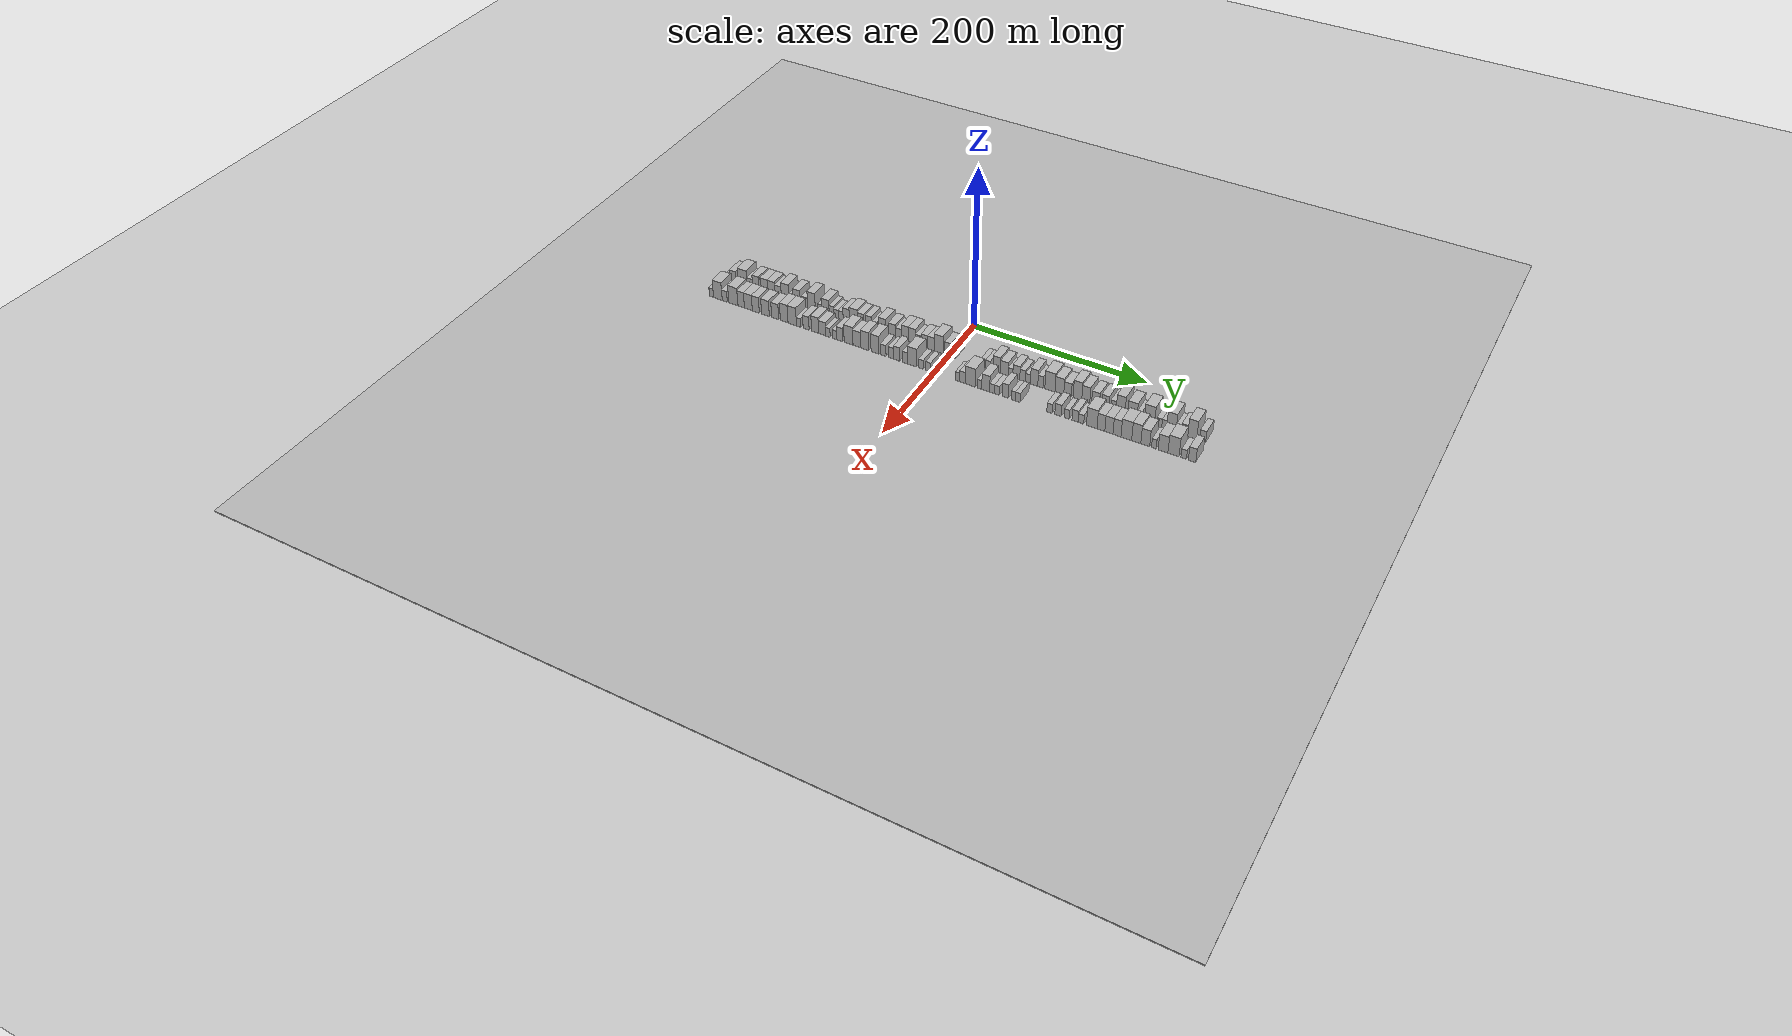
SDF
<?xml version="1.0" encoding="utf-8"?>

<sdf version="1.6">

   <world name="default">

      <gui fullscreen="0">

         <camera name="user_camera">

            <pose>-15 0 4.57585 0 0 0</pose>

            <view_controller>orbit</view_controller>

         </camera>

      </gui>

      <scene>

         <sky>

           <clouds>

             <speed>12</speed>

           </clouds>

         </sky>

         <ambient>0.4 0.4 0.4 1</ambient>

         <background>0.7 0.7 0.7 1</background>

         <shadows>1</shadows>

      </scene>

      <gravity>0 0 -9.8066</gravity>

      <magnetic_field>6e-06 2.3e-05 -4.2e-05</magnetic_field>

      <physics default="0" name="default_physics" type="ode">

         <ode>

            <solver>

               <type>quick</type>

               <iters>10</iters>

               <sor>1.0</sor>

               <use_dynamic_moi_rescaling>0</use_dynamic_moi_rescaling>

            </solver>

            <constraints>

               <cfm>0</cfm>

               <erp>0.2</erp>

               <contact_max_correcting_vel>100</contact_max_correcting_vel>

               <contact_surface_layer>0.001</contact_surface_layer>

            </constraints>

         </ode>

         <max_step_size>0.004</max_step_size>

         <real_time_factor>1</real_time_factor>

         <real_time_update_rate>250</real_time_update_rate>

      </physics>

      <light name="sun" type="directional">

         <cast_shadows>1</cast_shadows>

         <pose>0 0 10 0 0 0</pose>

         <diffuse>0.8 0.8 0.8 1</diffuse>

         <specular>0.2 0.2 0.2 1</specular>

         <attenuation>

            <range>1000</range>

            <constant>0.9</constant>

            <linear>0.01</linear>

            <quadratic>0.001</quadratic>

         </attenuation>

         <direction>-0.5 0.1 -0.9</direction>

      </light>

      <include>

         <name>ground_plane_1</name>

         <uri>model://HANNAS_ground_plane</uri>

         <pose>0 0 0  0 0 0</pose>

      </include>

      <include>

         <name>ground_plane_2</name>

         <uri>model://HANNAS_ground_plane</uri>

         <pose>100 0 0  0 0 0</pose>

      </include>

      <model name="building_1">

         <static>1</static>

         <pose frame="">50.0000 -278.3909 0 0.000000 0.000000 0.000000</pose>

         <link name="link">

            <pose frame="">0 0 6.00 0 0 0</pose>

            <collision name="collision">

               <geometry>

                  <box>

                     <size>20.0000 5.2182 12.0000</size>

                  </box>

               </geometry>

               <max_contacts>10</max_contacts>

               <surface>

                  <contact>

                     <ode/>

                  </contact>

                  <bounce/>

                  <friction>

                     <torsional>

                        <ode/>

                     </torsional>

                     <ode/>

                  </friction>

               </surface>

            </collision>

            <visual name="visual">

               <cast_shadows>0</cast_shadows>

               <geometry>

                  <box>

                     <size>20.0000 5.2182 12.0000</size>

                  </box>

               </geometry>

               <material>

                  <script>

                     <uri>model://HANNAS_wall/materials/scripts</uri>

                     <uri>model://HANNAS_wall/materials/textures</uri>

                     <name>vrc/HANNAS_wall</name>

                  </script>

               </material>

            </visual>

            <self_collide>0</self_collide>

            <enable_wind>0</enable_wind>

            <kinematic>0</kinematic>

         </link>

      </model>

      <model name="building_2">

         <static>1</static>

         <pose frame="">50.0000 -271.9759 0 0.000000 0.000000 0.000000</pose>

         <link name="link">

            <pose frame="">0 0 9.00 0 0 0</pose>

            <collision name="collision">

               <geometry>

                  <box>

                     <size>20.0000 7.6117 18.0000</size>

                  </box>

               </geometry>

               <max_contacts>10</max_contacts>

               <surface>

                  <contact>

                     <ode/>

                  </contact>

                  <bounce/>

                  <friction>

                     <torsional>

                        <ode/>

                     </torsional>

                     <ode/>

                  </friction>

               </surface>

            </collision>

            <visual name="visual">

               <cast_shadows>0</cast_shadows>

               <geometry>

                  <box>

                     <size>20.0000 7.6117 18.0000</size>

                  </box>

               </geometry>

               <material>

                  <script>

                     <uri>model://HANNAS_wall/materials/scripts</uri>

                     <uri>model://HANNAS_wall/materials/textures</uri>

                     <name>vrc/HANNAS_wall</name>

                  </script>

               </material>

            </visual>

            <self_collide>0</self_collide>

            <enable_wind>0</enable_wind>

            <kinematic>0</kinematic>

         </link>

      </model>

      <model name="building_3">

         <static>1</static>

         <pose frame="">50.0000 -259.2273 0 0.000000 0.000000 0.000000</pose>

         <link name="link">

            <pose frame="">0 0 12.00 0 0 0</pose>

            <collision name="collision">

               <geometry>

                  <box>

                     <size>20.0000 11.8855 24.0000</size>

                  </box>

               </geometry>

               <max_contacts>10</max_contacts>

               <surface>

                  <contact>

                     <ode/>

                  </contact>

                  <bounce/>

                  <friction>

                     <torsional>

                        <ode/>

                     </torsional>

                     <ode/>

                  </friction>

               </surface>

            </collision>

            <visual name="visual">

               <cast_shadows>0</cast_shadows>

               <geometry>

                  <box>

                     <size>20.0000 11.8855 24.0000</size>

                  </box>

               </geometry>

               <material>

                  <script>

                     <uri>model://HANNAS_wall/materials/scripts</uri>

                     <uri>model://HANNAS_wall/materials/textures</uri>

                     <name>vrc/HANNAS_wall</name>

                  </script>

               </material>

            </visual>

            <self_collide>0</self_collide>

            <enable_wind>0</enable_wind>

            <kinematic>0</kinematic>

         </link>

      </model>

      <model name="building_4">

         <static>1</static>

         <pose frame="">50.0000 -249.6853 0 0.000000 0.000000 0.000000</pose>

         <link name="link">

            <pose frame="">0 0 7.50 0 0 0</pose>

            <collision name="collision">

               <geometry>

                  <box>

                     <size>20.0000 7.1986 15.0000</size>

                  </box>

               </geometry>

               <max_contacts>10</max_contacts>

               <surface>

                  <contact>

                     <ode/>

                  </contact>

                  <bounce/>

                  <friction>

                     <torsional>

                        <ode/>

                     </torsional>

                     <ode/>

                  </friction>

               </surface>

            </collision>

            <visual name="visual">

               <cast_shadows>0</cast_shadows>

               <geometry>

                  <box>

                     <size>20.0000 7.1986 15.0000</size>

                  </box>

               </geometry>

               <material>

                  <script>

                     <uri>model://HANNAS_wall/materials/scripts</uri>

                     <uri>model://HANNAS_wall/materials/textures</uri>

                     <name>vrc/HANNAS_wall</name>

                  </script>

               </material>

            </visual>

            <self_collide>0</self_collide>

            <enable_wind>0</enable_wind>

            <kinematic>0</kinematic>

         </link>

      </model>

      <model name="building_5">

         <static>1</static>

         <pose frame="">50.0000 -241.8243 0 0.000000 0.000000 0.000000</pose>

         <link name="link">

            <pose frame="">0 0 10.50 0 0 0</pose>

            <collision name="collision">

               <geometry>

                  <box>

                     <size>20.0000 8.5234 21.0000</size>

                  </box>

               </geometry>

               <max_contacts>10</max_contacts>

               <surface>

                  <contact>

                     <ode/>

                  </contact>

                  <bounce/>

                  <friction>

                     <torsional>

                        <ode/>

                     </torsional>

                     <ode/>

                  </friction>

               </surface>

            </collision>

            <visual name="visual">

               <cast_shadows>0</cast_shadows>

               <geometry>

                  <box>

                     <size>20.0000 8.5234 21.0000</size>

                  </box>

               </geometry>

               <material>

                  <script>

                     <uri>model://HANNAS_wall/materials/scripts</uri>

                     <uri>model://HANNAS_wall/materials/textures</uri>

                     <name>vrc/HANNAS_wall</name>

                  </script>

               </material>

            </visual>

            <self_collide>0</self_collide>

            <enable_wind>0</enable_wind>

            <kinematic>0</kinematic>

         </link>

      </model>

      <model name="building_6">

         <static>1</static>

         <pose frame="">50.0000 -230.8683 0 0.000000 0.000000 0.000000</pose>

         <link name="link">

            <pose frame="">0 0 10.50 0 0 0</pose>

            <collision name="collision">

               <geometry>

                  <box>

                     <size>20.0000 9.3886 21.0000</size>

                  </box>

               </geometry>

               <max_contacts>10</max_contacts>

               <surface>

                  <contact>

                     <ode/>

                  </contact>

                  <bounce/>

                  <friction>

                     <torsional>

                        <ode/>

                     </torsional>

                     <ode/>

                  </friction>

               </surface>

            </collision>

            <visual name="visual">

               <cast_shadows>0</cast_shadows>

               <geometry>

                  <box>

                     <size>20.0000 9.3886 21.0000</size>

                  </box>

               </geometry>

               <material>

                  <script>

                     <uri>model://HANNAS_wall/materials/scripts</uri>

                     <uri>model://HANNAS_wall/materials/textures</uri>

                     <name>vrc/HANNAS_wall</name>

                  </script>

               </material>

            </visual>

            <self_collide>0</self_collide>

            <enable_wind>0</enable_wind>

            <kinematic>0</kinematic>

         </link>

      </model>

      <model name="building_7">

         <static>1</static>

         <pose frame="">50.0000 -221.6379 0 0.000000 0.000000 0.000000</pose>

         <link name="link">

            <pose frame="">0 0 10.50 0 0 0</pose>

            <collision name="collision">

               <geometry>

                  <box>

                     <size>20.0000 9.0723 21.0000</size>

                  </box>

               </geometry>

               <max_contacts>10</max_contacts>

               <surface>

                  <contact>

                     <ode/>

                  </contact>

                  <bounce/>

                  <friction>

                     <torsional>

                        <ode/>

                     </torsional>

                     <ode/>

                  </friction>

               </surface>

            </collision>

            <visual name="visual">

               <cast_shadows>0</cast_shadows>

               <geometry>

                  <box>

                     <size>20.0000 9.0723 21.0000</size>

                  </box>

               </geometry>

               <material>

                  <script>

                     <uri>model://HANNAS_wall/materials/scripts</uri>

                     <uri>model://HANNAS_wall/materials/textures</uri>

                     <name>vrc/HANNAS_wall</name>

                  </script>

               </material>

            </visual>

            <self_collide>0</self_collide>

            <enable_wind>0</enable_wind>

            <kinematic>0</kinematic>

         </link>

      </model>

      <model name="building_8">

         <static>1</static>

         <pose frame="">50.0000 -212.8523 0 0.000000 0.000000 0.000000</pose>

         <link name="link">

            <pose frame="">0 0 9.00 0 0 0</pose>

            <collision name="collision">

               <geometry>

                  <box>

                     <size>20.0000 8.4987 18.0000</size>

                  </box>

               </geometry>

               <max_contacts>10</max_contacts>

               <surface>

                  <contact>

                     <ode/>

                  </contact>

                  <bounce/>

                  <friction>

                     <torsional>

                        <ode/>

                     </torsional>

                     <ode/>

                  </friction>

               </surface>

            </collision>

            <visual name="visual">

               <cast_shadows>0</cast_shadows>

               <geometry>

                  <box>

                     <size>20.0000 8.4987 18.0000</size>

                  </box>

               </geometry>

               <material>

                  <script>

                     <uri>model://HANNAS_wall/materials/scripts</uri>

                     <uri>model://HANNAS_wall/materials/textures</uri>

                     <name>vrc/HANNAS_wall</name>

                  </script>

               </material>

            </visual>

            <self_collide>0</self_collide>

            <enable_wind>0</enable_wind>

            <kinematic>0</kinematic>

         </link>

      </model>

      <model name="building_9">

         <static>1</static>

         <pose frame="">50.0000 -203.7990 0 0.000000 0.000000 0.000000</pose>

         <link name="link">

            <pose frame="">0 0 12.00 0 0 0</pose>

            <collision name="collision">

               <geometry>

                  <box>

                     <size>20.0000 9.6079 24.0000</size>

                  </box>

               </geometry>

               <max_contacts>10</max_contacts>

               <surface>

                  <contact>

                     <ode/>

                  </contact>

                  <bounce/>

                  <friction>

                     <torsional>

                        <ode/>

                     </torsional>

                     <ode/>

                  </friction>

               </surface>

            </collision>

            <visual name="visual">

               <cast_shadows>0</cast_shadows>

               <geometry>

                  <box>

                     <size>20.0000 9.6079 24.0000</size>

                  </box>

               </geometry>

               <material>

                  <script>

                     <uri>model://HANNAS_wall/materials/scripts</uri>

                     <uri>model://HANNAS_wall/materials/textures</uri>

                     <name>vrc/HANNAS_wall</name>

                  </script>

               </material>

            </visual>

            <self_collide>0</self_collide>

            <enable_wind>0</enable_wind>

            <kinematic>0</kinematic>

         </link>

      </model>

      <model name="building_10">

         <static>1</static>

         <pose frame="">50.0000 -196.2178 0 0.000000 0.000000 0.000000</pose>

         <link name="link">

            <pose frame="">0 0 6.00 0 0 0</pose>

            <collision name="collision">

               <geometry>

                  <box>

                     <size>20.0000 5.5546 12.0000</size>

                  </box>

               </geometry>

               <max_contacts>10</max_contacts>

               <surface>

                  <contact>

                     <ode/>

                  </contact>

                  <bounce/>

                  <friction>

                     <torsional>

                        <ode/>

                     </torsional>

                     <ode/>

                  </friction>

               </surface>

            </collision>

            <visual name="visual">

               <cast_shadows>0</cast_shadows>

               <geometry>

                  <box>

                     <size>20.0000 5.5546 12.0000</size>

                  </box>

               </geometry>

               <material>

                  <script>

                     <uri>model://HANNAS_wall/materials/scripts</uri>

                     <uri>model://HANNAS_wall/materials/textures</uri>

                     <name>vrc/HANNAS_wall</name>

                  </script>

               </material>

            </visual>

            <self_collide>0</self_collide>

            <enable_wind>0</enable_wind>

            <kinematic>0</kinematic>

         </link>

      </model>

      <model name="building_11">

         <static>1</static>

         <pose frame="">50.0000 -188.8204 0 0.000000 0.000000 0.000000</pose>

         <link name="link">

            <pose frame="">0 0 10.50 0 0 0</pose>

            <collision name="collision">

               <geometry>

                  <box>

                     <size>20.0000 9.2402 21.0000</size>

                  </box>

               </geometry>

               <max_contacts>10</max_contacts>

               <surface>

                  <contact>

                     <ode/>

                  </contact>

                  <bounce/>

                  <friction>

                     <torsional>

                        <ode/>

                     </torsional>

                     <ode/>

                  </friction>

               </surface>

            </collision>

            <visual name="visual">

               <cast_shadows>0</cast_shadows>

               <geometry>

                  <box>

                     <size>20.0000 9.2402 21.0000</size>

                  </box>

               </geometry>

               <material>

                  <script>

                     <uri>model://HANNAS_wall/materials/scripts</uri>

                     <uri>model://HANNAS_wall/materials/textures</uri>

                     <name>vrc/HANNAS_wall</name>

                  </script>

               </material>

            </visual>

            <self_collide>0</self_collide>

            <enable_wind>0</enable_wind>

            <kinematic>0</kinematic>

         </link>

      </model>

      <model name="building_12">

         <static>1</static>

         <pose frame="">50.0000 -178.4922 0 0.000000 0.000000 0.000000</pose>

         <link name="link">

            <pose frame="">0 0 7.50 0 0 0</pose>

            <collision name="collision">

               <geometry>

                  <box>

                     <size>20.0000 7.4162 15.0000</size>

                  </box>

               </geometry>

               <max_contacts>10</max_contacts>

               <surface>

                  <contact>

                     <ode/>

                  </contact>

                  <bounce/>

                  <friction>

                     <torsional>

                        <ode/>

                     </torsional>

                     <ode/>

                  </friction>

               </surface>

            </collision>

            <visual name="visual">

               <cast_shadows>0</cast_shadows>

               <geometry>

                  <box>

                     <size>20.0000 7.4162 15.0000</size>

                  </box>

               </geometry>

               <material>

                  <script>

                     <uri>model://HANNAS_wall/materials/scripts</uri>

                     <uri>model://HANNAS_wall/materials/textures</uri>

                     <name>vrc/HANNAS_wall</name>

                  </script>

               </material>

            </visual>

            <self_collide>0</self_collide>

            <enable_wind>0</enable_wind>

            <kinematic>0</kinematic>

         </link>

      </model>

      <model name="building_13">

         <static>1</static>

         <pose frame="">50.0000 -169.9375 0 0.000000 0.000000 0.000000</pose>

         <link name="link">

            <pose frame="">0 0 12.00 0 0 0</pose>

            <collision name="collision">

               <geometry>

                  <box>

                     <size>20.0000 9.6934 24.0000</size>

                  </box>

               </geometry>

               <max_contacts>10</max_contacts>

               <surface>

                  <contact>

                     <ode/>

                  </contact>

                  <bounce/>

                  <friction>

                     <torsional>

                        <ode/>

                     </torsional>

                     <ode/>

                  </friction>

               </surface>

            </collision>

            <visual name="visual">

               <cast_shadows>0</cast_shadows>

               <geometry>

                  <box>

                     <size>20.0000 9.6934 24.0000</size>

                  </box>

               </geometry>

               <material>

                  <script>

                     <uri>model://HANNAS_wall/materials/scripts</uri>

                     <uri>model://HANNAS_wall/materials/textures</uri>

                     <name>vrc/HANNAS_wall</name>

                  </script>

               </material>

            </visual>

            <self_collide>0</self_collide>

            <enable_wind>0</enable_wind>

            <kinematic>0</kinematic>

         </link>

      </model>

      <model name="building_14">

         <static>1</static>

         <pose frame="">50.0000 -159.5936 0 0.000000 0.000000 0.000000</pose>

         <link name="link">

            <pose frame="">0 0 6.00 0 0 0</pose>

            <collision name="collision">

               <geometry>

                  <box>

                     <size>20.0000 4.9944 12.0000</size>

                  </box>

               </geometry>

               <max_contacts>10</max_contacts>

               <surface>

                  <contact>

                     <ode/>

                  </contact>

                  <bounce/>

                  <friction>

                     <torsional>

                        <ode/>

                     </torsional>

                     <ode/>

                  </friction>

               </surface>

            </collision>

            <visual name="visual">

               <cast_shadows>0</cast_shadows>

               <geometry>

                  <box>

                     <size>20.0000 4.9944 12.0000</size>

                  </box>

               </geometry>

               <material>

                  <script>

                     <uri>model://HANNAS_wall/materials/scripts</uri>

                     <uri>model://HANNAS_wall/materials/textures</uri>

                     <name>vrc/HANNAS_wall</name>

                  </script>

               </material>

            </visual>

            <self_collide>0</self_collide>

            <enable_wind>0</enable_wind>

            <kinematic>0</kinematic>

         </link>

      </model>

      <model name="building_15">

         <static>1</static>

         <pose frame="">50.0000 -152.2584 0 0.000000 0.000000 0.000000</pose>

         <link name="link">

            <pose frame="">0 0 10.50 0 0 0</pose>

            <collision name="collision">

               <geometry>

                  <box>

                     <size>20.0000 9.6758 21.0000</size>

                  </box>

               </geometry>

               <max_contacts>10</max_contacts>

               <surface>

                  <contact>

                     <ode/>

                  </contact>

                  <bounce/>

                  <friction>

                     <torsional>

                        <ode/>

                     </torsional>

                     <ode/>

                  </friction>

               </surface>

            </collision>

            <visual name="visual">

               <cast_shadows>0</cast_shadows>

               <geometry>

                  <box>

                     <size>20.0000 9.6758 21.0000</size>

                  </box>

               </geometry>

               <material>

                  <script>

                     <uri>model://HANNAS_wall/materials/scripts</uri>

                     <uri>model://HANNAS_wall/materials/textures</uri>

                     <name>vrc/HANNAS_wall</name>

                  </script>

               </material>

            </visual>

            <self_collide>0</self_collide>

            <enable_wind>0</enable_wind>

            <kinematic>0</kinematic>

         </link>

      </model>

      <model name="building_16">

         <static>1</static>

         <pose frame="">50.0000 -144.3793 0 0.000000 0.000000 0.000000</pose>

         <link name="link">

            <pose frame="">0 0 7.50 0 0 0</pose>

            <collision name="collision">

               <geometry>

                  <box>

                     <size>20.0000 6.0824 15.0000</size>

                  </box>

               </geometry>

               <max_contacts>10</max_contacts>

               <surface>

                  <contact>

                     <ode/>

                  </contact>

                  <bounce/>

                  <friction>

                     <torsional>

                        <ode/>

                     </torsional>

                     <ode/>

                  </friction>

               </surface>

            </collision>

            <visual name="visual">

               <cast_shadows>0</cast_shadows>

               <geometry>

                  <box>

                     <size>20.0000 6.0824 15.0000</size>

                  </box>

               </geometry>

               <material>

                  <script>

                     <uri>model://HANNAS_wall/materials/scripts</uri>

                     <uri>model://HANNAS_wall/materials/textures</uri>

                     <name>vrc/HANNAS_wall</name>

                  </script>

               </material>

            </visual>

            <self_collide>0</self_collide>

            <enable_wind>0</enable_wind>

            <kinematic>0</kinematic>

         </link>

      </model>

      <model name="building_17">

         <static>1</static>

         <pose frame="">50.0000 -138.5889 0 0.000000 0.000000 0.000000</pose>

         <link name="link">

            <pose frame="">0 0 6.00 0 0 0</pose>

            <collision name="collision">

               <geometry>

                  <box>

                     <size>20.0000 5.4985 12.0000</size>

                  </box>

               </geometry>

               <max_contacts>10</max_contacts>

               <surface>

                  <contact>

                     <ode/>

                  </contact>

                  <bounce/>

                  <friction>

                     <torsional>

                        <ode/>

                     </torsional>

                     <ode/>

                  </friction>

               </surface>

            </collision>

            <visual name="visual">

               <cast_shadows>0</cast_shadows>

               <geometry>

                  <box>

                     <size>20.0000 5.4985 12.0000</size>

                  </box>

               </geometry>

               <material>

                  <script>

                     <uri>model://HANNAS_wall/materials/scripts</uri>

                     <uri>model://HANNAS_wall/materials/textures</uri>

                     <name>vrc/HANNAS_wall</name>

                  </script>

               </material>

            </visual>

            <self_collide>0</self_collide>

            <enable_wind>0</enable_wind>

            <kinematic>0</kinematic>

         </link>

      </model>

      <model name="building_18">

         <static>1</static>

         <pose frame="">50.0000 -132.8439 0 0.000000 0.000000 0.000000</pose>

         <link name="link">

            <pose frame="">0 0 6.00 0 0 0</pose>

            <collision name="collision">

               <geometry>

                  <box>

                     <size>20.0000 5.9916 12.0000</size>

                  </box>

               </geometry>

               <max_contacts>10</max_contacts>

               <surface>

                  <contact>

                     <ode/>

                  </contact>

                  <bounce/>

                  <friction>

                     <torsional>

                        <ode/>

                     </torsional>

                     <ode/>

                  </friction>

               </surface>

            </collision>

            <visual name="visual">

               <cast_shadows>0</cast_shadows>

               <geometry>

                  <box>

                     <size>20.0000 5.9916 12.0000</size>

                  </box>

               </geometry>

               <material>

                  <script>

                     <uri>model://HANNAS_wall/materials/scripts</uri>

                     <uri>model://HANNAS_wall/materials/textures</uri>

                     <name>vrc/HANNAS_wall</name>

                  </script>

               </material>

            </visual>

            <self_collide>0</self_collide>

            <enable_wind>0</enable_wind>

            <kinematic>0</kinematic>

         </link>

      </model>

      <model name="building_19">

         <static>1</static>

         <pose frame="">50.0000 -125.9320 0 0.000000 0.000000 0.000000</pose>

         <link name="link">

            <pose frame="">0 0 9.00 0 0 0</pose>

            <collision name="collision">

               <geometry>

                  <box>

                     <size>20.0000 7.8322 18.0000</size>

                  </box>

               </geometry>

               <max_contacts>10</max_contacts>

               <surface>

                  <contact>

                     <ode/>

                  </contact>

                  <bounce/>

                  <friction>

                     <torsional>

                        <ode/>

                     </torsional>

                     <ode/>

                  </friction>

               </surface>

            </collision>

            <visual name="visual">

               <cast_shadows>0</cast_shadows>

               <geometry>

                  <box>

                     <size>20.0000 7.8322 18.0000</size>

                  </box>

               </geometry>

               <material>

                  <script>

                     <uri>model://HANNAS_wall/materials/scripts</uri>

                     <uri>model://HANNAS_wall/materials/textures</uri>

                     <name>vrc/HANNAS_wall</name>

                  </script>

               </material>

            </visual>

            <self_collide>0</self_collide>

            <enable_wind>0</enable_wind>

            <kinematic>0</kinematic>

         </link>

      </model>

      <model name="building_20">

         <static>1</static>

         <pose frame="">50.0000 -116.9215 0 0.000000 0.000000 0.000000</pose>

         <link name="link">

            <pose frame="">0 0 10.50 0 0 0</pose>

            <collision name="collision">

               <geometry>

                  <box>

                     <size>20.0000 10.1887 21.0000</size>

                  </box>

               </geometry>

               <max_contacts>10</max_contacts>

               <surface>

                  <contact>

                     <ode/>

                  </contact>

                  <bounce/>

                  <friction>

                     <torsional>

                        <ode/>

                     </torsional>

                     <ode/>

                  </friction>

               </surface>

            </collision>

            <visual name="visual">

               <cast_shadows>0</cast_shadows>

               <geometry>

                  <box>

                     <size>20.0000 10.1887 21.0000</size>

                  </box>

               </geometry>

               <material>

                  <script>

                     <uri>model://HANNAS_wall/materials/scripts</uri>

                     <uri>model://HANNAS_wall/materials/textures</uri>

                     <name>vrc/HANNAS_wall</name>

                  </script>

               </material>

            </visual>

            <self_collide>0</self_collide>

            <enable_wind>0</enable_wind>

            <kinematic>0</kinematic>

         </link>

      </model>

      <model name="building_21">

         <static>1</static>

         <pose frame="">50.0000 -107.7564 0 0.000000 0.000000 0.000000</pose>

         <link name="link">

            <pose frame="">0 0 9.00 0 0 0</pose>

            <collision name="collision">

               <geometry>

                  <box>

                     <size>20.0000 8.1417 18.0000</size>

                  </box>

               </geometry>

               <max_contacts>10</max_contacts>

               <surface>

                  <contact>

                     <ode/>

                  </contact>

                  <bounce/>

                  <friction>

                     <torsional>

                        <ode/>

                     </torsional>

                     <ode/>

                  </friction>

               </surface>

            </collision>

            <visual name="visual">

               <cast_shadows>0</cast_shadows>

               <geometry>

                  <box>

                     <size>20.0000 8.1417 18.0000</size>

                  </box>

               </geometry>

               <material>

                  <script>

                     <uri>model://HANNAS_wall/materials/scripts</uri>

                     <uri>model://HANNAS_wall/materials/textures</uri>

                     <name>vrc/HANNAS_wall</name>

                  </script>

               </material>

            </visual>

            <self_collide>0</self_collide>

            <enable_wind>0</enable_wind>

            <kinematic>0</kinematic>

         </link>

      </model>

      <model name="building_22">

         <static>1</static>

         <pose frame="">50.0000 -97.9635 0 0.000000 0.000000 0.000000</pose>

         <link name="link">

            <pose frame="">0 0 9.00 0 0 0</pose>

            <collision name="collision">

               <geometry>

                  <box>

                     <size>20.0000 7.4440 18.0000</size>

                  </box>

               </geometry>

               <max_contacts>10</max_contacts>

               <surface>

                  <contact>

                     <ode/>

                  </contact>

                  <bounce/>

                  <friction>

                     <torsional>

                        <ode/>

                     </torsional>

                     <ode/>

                  </friction>

               </surface>

            </collision>

            <visual name="visual">

               <cast_shadows>0</cast_shadows>

               <geometry>

                  <box>

                     <size>20.0000 7.4440 18.0000</size>

                  </box>

               </geometry>

               <material>

                  <script>

                     <uri>model://HANNAS_wall/materials/scripts</uri>

                     <uri>model://HANNAS_wall/materials/textures</uri>

                     <name>vrc/HANNAS_wall</name>

                  </script>

               </material>

            </visual>

            <self_collide>0</self_collide>

            <enable_wind>0</enable_wind>

            <kinematic>0</kinematic>

         </link>

      </model>

      <model name="building_23">

         <static>1</static>

         <pose frame="">50.0000 -91.5334 0 0.000000 0.000000 0.000000</pose>

         <link name="link">

            <pose frame="">0 0 6.00 0 0 0</pose>

            <collision name="collision">

               <geometry>

                  <box>

                     <size>20.0000 5.4163 12.0000</size>

                  </box>

               </geometry>

               <max_contacts>10</max_contacts>

               <surface>

                  <contact>

                     <ode/>

                  </contact>

                  <bounce/>

                  <friction>

                     <torsional>

                        <ode/>

                     </torsional>

                     <ode/>

                  </friction>

               </surface>

            </collision>

            <visual name="visual">

               <cast_shadows>0</cast_shadows>

               <geometry>

                  <box>

                     <size>20.0000 5.4163 12.0000</size>

                  </box>

               </geometry>

               <material>

                  <script>

                     <uri>model://HANNAS_wall/materials/scripts</uri>

                     <uri>model://HANNAS_wall/materials/textures</uri>

                     <name>vrc/HANNAS_wall</name>

                  </script>

               </material>

            </visual>

            <self_collide>0</self_collide>

            <enable_wind>0</enable_wind>

            <kinematic>0</kinematic>

         </link>

      </model>

      <model name="building_24">

         <static>1</static>

         <pose frame="">50.0000 -81.1538 0 0.000000 0.000000 0.000000</pose>

         <link name="link">

            <pose frame="">0 0 10.50 0 0 0</pose>

            <collision name="collision">

               <geometry>

                  <box>

                     <size>20.0000 9.3428 21.0000</size>

                  </box>

               </geometry>

               <max_contacts>10</max_contacts>

               <surface>

                  <contact>

                     <ode/>

                  </contact>

                  <bounce/>

                  <friction>

                     <torsional>

                        <ode/>

                     </torsional>

                     <ode/>

                  </friction>

               </surface>

            </collision>

            <visual name="visual">

               <cast_shadows>0</cast_shadows>

               <geometry>

                  <box>

                     <size>20.0000 9.3428 21.0000</size>

                  </box>

               </geometry>

               <material>

                  <script>

                     <uri>model://HANNAS_wall/materials/scripts</uri>

                     <uri>model://HANNAS_wall/materials/textures</uri>

                     <name>vrc/HANNAS_wall</name>

                  </script>

               </material>

            </visual>

            <self_collide>0</self_collide>

            <enable_wind>0</enable_wind>

            <kinematic>0</kinematic>

         </link>

      </model>

      <model name="building_25">

         <static>1</static>

         <pose frame="">50.0000 -69.0168 0 0.000000 0.000000 0.000000</pose>

         <link name="link">

            <pose frame="">0 0 9.00 0 0 0</pose>

            <collision name="collision">

               <geometry>

                  <box>

                     <size>20.0000 8.9312 18.0000</size>

                  </box>

               </geometry>

               <max_contacts>10</max_contacts>

               <surface>

                  <contact>

                     <ode/>

                  </contact>

                  <bounce/>

                  <friction>

                     <torsional>

                        <ode/>

                     </torsional>

                     <ode/>

                  </friction>

               </surface>

            </collision>

            <visual name="visual">

               <cast_shadows>0</cast_shadows>

               <geometry>

                  <box>

                     <size>20.0000 8.9312 18.0000</size>

                  </box>

               </geometry>

               <material>

                  <script>

                     <uri>model://HANNAS_wall/materials/scripts</uri>

                     <uri>model://HANNAS_wall/materials/textures</uri>

                     <name>vrc/HANNAS_wall</name>

                  </script>

               </material>

            </visual>

            <self_collide>0</self_collide>

            <enable_wind>0</enable_wind>

            <kinematic>0</kinematic>

         </link>

      </model>

      <model name="building_26">

         <static>1</static>

         <pose frame="">50.0000 -61.0077 0 0.000000 0.000000 0.000000</pose>

         <link name="link">

            <pose frame="">0 0 7.50 0 0 0</pose>

            <collision name="collision">

               <geometry>

                  <box>

                     <size>20.0000 7.0871 15.0000</size>

                  </box>

               </geometry>

               <max_contacts>10</max_contacts>

               <surface>

                  <contact>

                     <ode/>

                  </contact>

                  <bounce/>

                  <friction>

                     <torsional>

                        <ode/>

                     </torsional>

                     <ode/>

                  </friction>

               </surface>

            </collision>

            <visual name="visual">

               <cast_shadows>0</cast_shadows>

               <geometry>

                  <box>

                     <size>20.0000 7.0871 15.0000</size>

                  </box>

               </geometry>

               <material>

                  <script>

                     <uri>model://HANNAS_wall/materials/scripts</uri>

                     <uri>model://HANNAS_wall/materials/textures</uri>

                     <name>vrc/HANNAS_wall</name>

                  </script>

               </material>

            </visual>

            <self_collide>0</self_collide>

            <enable_wind>0</enable_wind>

            <kinematic>0</kinematic>

         </link>

      </model>

      <model name="building_27">

         <static>1</static>

         <pose frame="">50.0000 -53.2156 0 0.000000 0.000000 0.000000</pose>

         <link name="link">

            <pose frame="">0 0 10.50 0 0 0</pose>

            <collision name="collision">

               <geometry>

                  <box>

                     <size>20.0000 8.4971 21.0000</size>

                  </box>

               </geometry>

               <max_contacts>10</max_contacts>

               <surface>

                  <contact>

                     <ode/>

                  </contact>

                  <bounce/>

                  <friction>

                     <torsional>

                        <ode/>

                     </torsional>

                     <ode/>

                  </friction>

               </surface>

            </collision>

            <visual name="visual">

               <cast_shadows>0</cast_shadows>

               <geometry>

                  <box>

                     <size>20.0000 8.4971 21.0000</size>

                  </box>

               </geometry>

               <material>

                  <script>

                     <uri>model://HANNAS_wall/materials/scripts</uri>

                     <uri>model://HANNAS_wall/materials/textures</uri>

                     <name>vrc/HANNAS_wall</name>

                  </script>

               </material>

            </visual>

            <self_collide>0</self_collide>

            <enable_wind>0</enable_wind>

            <kinematic>0</kinematic>

         </link>

      </model>

      <model name="building_28">

         <static>1</static>

         <pose frame="">50.0000 -44.6585 0 0.000000 0.000000 0.000000</pose>

         <link name="link">

            <pose frame="">0 0 10.50 0 0 0</pose>

            <collision name="collision">

               <geometry>

                  <box>

                     <size>20.0000 8.6171 21.0000</size>

                  </box>

               </geometry>

               <max_contacts>10</max_contacts>

               <surface>

                  <contact>

                     <ode/>

                  </contact>

                  <bounce/>

                  <friction>

                     <torsional>

                        <ode/>

                     </torsional>

                     <ode/>

                  </friction>

               </surface>

            </collision>

            <visual name="visual">

               <cast_shadows>0</cast_shadows>

               <geometry>

                  <box>

                     <size>20.0000 8.6171 21.0000</size>

                  </box>

               </geometry>

               <material>

                  <script>

                     <uri>model://HANNAS_wall/materials/scripts</uri>

                     <uri>model://HANNAS_wall/materials/textures</uri>

                     <name>vrc/HANNAS_wall</name>

                  </script>

               </material>

            </visual>

            <self_collide>0</self_collide>

            <enable_wind>0</enable_wind>

            <kinematic>0</kinematic>

         </link>

      </model>

      <model name="building_29">

         <static>1</static>

         <pose frame="">50.0000 -36.8754 0 0.000000 0.000000 0.000000</pose>

         <link name="link">

            <pose frame="">0 0 7.50 0 0 0</pose>

            <collision name="collision">

               <geometry>

                  <box>

                     <size>20.0000 6.9492 15.0000</size>

                  </box>

               </geometry>

               <max_contacts>10</max_contacts>

               <surface>

                  <contact>

                     <ode/>

                  </contact>

                  <bounce/>

                  <friction>

                     <torsional>

                        <ode/>

                     </torsional>

                     <ode/>

                  </friction>

               </surface>

            </collision>

            <visual name="visual">

               <cast_shadows>0</cast_shadows>

               <geometry>

                  <box>

                     <size>20.0000 6.9492 15.0000</size>

                  </box>

               </geometry>

               <material>

                  <script>

                     <uri>model://HANNAS_wall/materials/scripts</uri>

                     <uri>model://HANNAS_wall/materials/textures</uri>

                     <name>vrc/HANNAS_wall</name>

                  </script>

               </material>

            </visual>

            <self_collide>0</self_collide>

            <enable_wind>0</enable_wind>

            <kinematic>0</kinematic>

         </link>

      </model>

      <model name="building_30">

         <static>1</static>

         <pose frame="">50.0000 -29.5165 0 0.000000 0.000000 0.000000</pose>

         <link name="link">

            <pose frame="">0 0 9.00 0 0 0</pose>

            <collision name="collision">

               <geometry>

                  <box>

                     <size>20.0000 7.7685 18.0000</size>

                  </box>

               </geometry>

               <max_contacts>10</max_contacts>

               <surface>

                  <contact>

                     <ode/>

                  </contact>

                  <bounce/>

                  <friction>

                     <torsional>

                        <ode/>

                     </torsional>

                     <ode/>

                  </friction>

               </surface>

            </collision>

            <visual name="visual">

               <cast_shadows>0</cast_shadows>

               <geometry>

                  <box>

                     <size>20.0000 7.7685 18.0000</size>

                  </box>

               </geometry>

               <material>

                  <script>

                     <uri>model://HANNAS_wall/materials/scripts</uri>

                     <uri>model://HANNAS_wall/materials/textures</uri>

                     <name>vrc/HANNAS_wall</name>

                  </script>

               </material>

            </visual>

            <self_collide>0</self_collide>

            <enable_wind>0</enable_wind>

            <kinematic>0</kinematic>

         </link>

      </model>

      <model name="building_31">

         <static>1</static>

         <pose frame="">50.0000 -21.8159 0 0.000000 0.000000 0.000000</pose>

         <link name="link">

            <pose frame="">0 0 9.00 0 0 0</pose>

            <collision name="collision">

               <geometry>

                  <box>

                     <size>20.0000 7.6327 18.0000</size>

                  </box>

               </geometry>

               <max_contacts>10</max_contacts>

               <surface>

                  <contact>

                     <ode/>

                  </contact>

                  <bounce/>

                  <friction>

                     <torsional>

                        <ode/>

                     </torsional>

                     <ode/>

                  </friction>

               </surface>

            </collision>

            <visual name="visual">

               <cast_shadows>0</cast_shadows>

               <geometry>

                  <box>

                     <size>20.0000 7.6327 18.0000</size>

                  </box>

               </geometry>

               <material>

                  <script>

                     <uri>model://HANNAS_wall/materials/scripts</uri>

                     <uri>model://HANNAS_wall/materials/textures</uri>

                     <name>vrc/HANNAS_wall</name>

                  </script>

               </material>

            </visual>

            <self_collide>0</self_collide>

            <enable_wind>0</enable_wind>

            <kinematic>0</kinematic>

         </link>

      </model>

      <model name="building_32">

         <static>1</static>

         <pose frame="">50.0000 -12.5680 0 0.000000 0.000000 0.000000</pose>

         <link name="link">

            <pose frame="">0 0 12.00 0 0 0</pose>

            <collision name="collision">

               <geometry>

                  <box>

                     <size>20.0000 10.8629 24.0000</size>

                  </box>

               </geometry>

               <max_contacts>10</max_contacts>

               <surface>

                  <contact>

                     <ode/>

                  </contact>

                  <bounce/>

                  <friction>

                     <torsional>

                        <ode/>

                     </torsional>

                     <ode/>

                  </friction>

               </surface>

            </collision>

            <visual name="visual">

               <cast_shadows>0</cast_shadows>

               <geometry>

                  <box>

                     <size>20.0000 10.8629 24.0000</size>

                  </box>

               </geometry>

               <material>

                  <script>

                     <uri>model://HANNAS_wall/materials/scripts</uri>

                     <uri>model://HANNAS_wall/materials/textures</uri>

                     <name>vrc/HANNAS_wall</name>

                  </script>

               </material>

            </visual>

            <self_collide>0</self_collide>

            <enable_wind>0</enable_wind>

            <kinematic>0</kinematic>

         </link>

      </model>

      <model name="building_33">

         <static>1</static>

         <pose frame="">50.0000 -1.3900 0 0.000000 0.000000 0.000000</pose>

         <link name="link">

            <pose frame="">0 0 9.00 0 0 0</pose>

            <collision name="collision">

               <geometry>

                  <box>

                     <size>20.0000 7.4931 18.0000</size>

                  </box>

               </geometry>

               <max_contacts>10</max_contacts>

               <surface>

                  <contact>

                     <ode/>

                  </contact>

                  <bounce/>

                  <friction>

                     <torsional>

                        <ode/>

                     </torsional>

                     <ode/>

                  </friction>

               </surface>

            </collision>

            <visual name="visual">

               <cast_shadows>0</cast_shadows>

               <geometry>

                  <box>

                     <size>20.0000 7.4931 18.0000</size>

                  </box>

               </geometry>

               <material>

                  <script>

                     <uri>model://HANNAS_wall/materials/scripts</uri>

                     <uri>model://HANNAS_wall/materials/textures</uri>

                     <name>vrc/HANNAS_wall</name>

                  </script>

               </material>

            </visual>

            <self_collide>0</self_collide>

            <enable_wind>0</enable_wind>

            <kinematic>0</kinematic>

         </link>

      </model>

      <model name="building_34">

         <static>1</static>

         <pose frame="">50.0000 5.2241 0 0.000000 0.000000 0.000000</pose>

         <link name="link">

            <pose frame="">0 0 6.00 0 0 0</pose>

            <collision name="collision">

               <geometry>

                  <box>

                     <size>20.0000 5.7352 12.0000</size>

                  </box>

               </geometry>

               <max_contacts>10</max_contacts>

               <surface>

                  <contact>

                     <ode/>

                  </contact>

                  <bounce/>

                  <friction>

                     <torsional>

                        <ode/>

                     </torsional>

                     <ode/>

                  </friction>

               </surface>

            </collision>

            <visual name="visual">

               <cast_shadows>0</cast_shadows>

               <geometry>

                  <box>

                     <size>20.0000 5.7352 12.0000</size>

                  </box>

               </geometry>

               <material>

                  <script>

                     <uri>model://HANNAS_wall/materials/scripts</uri>

                     <uri>model://HANNAS_wall/materials/textures</uri>

                     <name>vrc/HANNAS_wall</name>

                  </script>

               </material>

            </visual>

            <self_collide>0</self_collide>

            <enable_wind>0</enable_wind>

            <kinematic>0</kinematic>

         </link>

      </model>

      <model name="building_35">

         <static>1</static>

         <pose frame="">50.0000 40.5400 0 0.000000 0.000000 0.000000</pose>

         <link name="link">

            <pose frame="">0 0 6.00 0 0 0</pose>

            <collision name="collision">

               <geometry>

                  <box>

                     <size>20.0000 5.6322 12.0000</size>

                  </box>

               </geometry>

               <max_contacts>10</max_contacts>

               <surface>

                  <contact>

                     <ode/>

                  </contact>

                  <bounce/>

                  <friction>

                     <torsional>

                        <ode/>

                     </torsional>

                     <ode/>

                  </friction>

               </surface>

            </collision>

            <visual name="visual">

               <cast_shadows>0</cast_shadows>

               <geometry>

                  <box>

                     <size>20.0000 5.6322 12.0000</size>

                  </box>

               </geometry>

               <material>

                  <script>

                     <uri>model://HANNAS_wall/materials/scripts</uri>

                     <uri>model://HANNAS_wall/materials/textures</uri>

                     <name>vrc/HANNAS_wall</name>

                  </script>

               </material>

            </visual>

            <self_collide>0</self_collide>

            <enable_wind>0</enable_wind>

            <kinematic>0</kinematic>

         </link>

      </model>

      <model name="building_36">

         <static>1</static>

         <pose frame="">50.0000 45.9921 0 0.000000 0.000000 0.000000</pose>

         <link name="link">

            <pose frame="">0 0 6.00 0 0 0</pose>

            <collision name="collision">

               <geometry>

                  <box>

                     <size>20.0000 5.2721 12.0000</size>

                  </box>

               </geometry>

               <max_contacts>10</max_contacts>

               <surface>

                  <contact>

                     <ode/>

                  </contact>

                  <bounce/>

                  <friction>

                     <torsional>

                        <ode/>

                     </torsional>

                     <ode/>

                  </friction>

               </surface>

            </collision>

            <visual name="visual">

               <cast_shadows>0</cast_shadows>

               <geometry>

                  <box>

                     <size>20.0000 5.2721 12.0000</size>

                  </box>

               </geometry>

               <material>

                  <script>

                     <uri>model://HANNAS_wall/materials/scripts</uri>

                     <uri>model://HANNAS_wall/materials/textures</uri>

                     <name>vrc/HANNAS_wall</name>

                  </script>

               </material>

            </visual>

            <self_collide>0</self_collide>

            <enable_wind>0</enable_wind>

            <kinematic>0</kinematic>

         </link>

      </model>

      <model name="building_37">

         <static>1</static>

         <pose frame="">50.0000 56.0227 0 0.000000 0.000000 0.000000</pose>

         <link name="link">

            <pose frame="">0 0 10.50 0 0 0</pose>

            <collision name="collision">

               <geometry>

                  <box>

                     <size>20.0000 8.7891 21.0000</size>

                  </box>

               </geometry>

               <max_contacts>10</max_contacts>

               <surface>

                  <contact>

                     <ode/>

                  </contact>

                  <bounce/>

                  <friction>

                     <torsional>

                        <ode/>

                     </torsional>

                     <ode/>

                  </friction>

               </surface>

            </collision>

            <visual name="visual">

               <cast_shadows>0</cast_shadows>

               <geometry>

                  <box>

                     <size>20.0000 8.7891 21.0000</size>

                  </box>

               </geometry>

               <material>

                  <script>

                     <uri>model://HANNAS_wall/materials/scripts</uri>

                     <uri>model://HANNAS_wall/materials/textures</uri>

                     <name>vrc/HANNAS_wall</name>

                  </script>

               </material>

            </visual>

            <self_collide>0</self_collide>

            <enable_wind>0</enable_wind>

            <kinematic>0</kinematic>

         </link>

      </model>

      <model name="building_38">

         <static>1</static>

         <pose frame="">50.0000 64.8491 0 0.000000 0.000000 0.000000</pose>

         <link name="link">

            <pose frame="">0 0 9.00 0 0 0</pose>

            <collision name="collision">

               <geometry>

                  <box>

                     <size>20.0000 8.8636 18.0000</size>

                  </box>

               </geometry>

               <max_contacts>10</max_contacts>

               <surface>

                  <contact>

                     <ode/>

                  </contact>

                  <bounce/>

                  <friction>

                     <torsional>

                        <ode/>

                     </torsional>

                     <ode/>

                  </friction>

               </surface>

            </collision>

            <visual name="visual">

               <cast_shadows>0</cast_shadows>

               <geometry>

                  <box>

                     <size>20.0000 8.8636 18.0000</size>

                  </box>

               </geometry>

               <material>

                  <script>

                     <uri>model://HANNAS_wall/materials/scripts</uri>

                     <uri>model://HANNAS_wall/materials/textures</uri>

                     <name>vrc/HANNAS_wall</name>

                  </script>

               </material>

            </visual>

            <self_collide>0</self_collide>

            <enable_wind>0</enable_wind>

            <kinematic>0</kinematic>

         </link>

      </model>

      <model name="building_39">

         <static>1</static>

         <pose frame="">50.0000 71.9994 0 0.000000 0.000000 0.000000</pose>

         <link name="link">

            <pose frame="">0 0 6.00 0 0 0</pose>

            <collision name="collision">

               <geometry>

                  <box>

                     <size>20.0000 5.4370 12.0000</size>

                  </box>

               </geometry>

               <max_contacts>10</max_contacts>

               <surface>

                  <contact>

                     <ode/>

                  </contact>

                  <bounce/>

                  <friction>

                     <torsional>

                        <ode/>

                     </torsional>

                     <ode/>

                  </friction>

               </surface>

            </collision>

            <visual name="visual">

               <cast_shadows>0</cast_shadows>

               <geometry>

                  <box>

                     <size>20.0000 5.4370 12.0000</size>

                  </box>

               </geometry>

               <material>

                  <script>

                     <uri>model://HANNAS_wall/materials/scripts</uri>

                     <uri>model://HANNAS_wall/materials/textures</uri>

                     <name>vrc/HANNAS_wall</name>

                  </script>

               </material>

            </visual>

            <self_collide>0</self_collide>

            <enable_wind>0</enable_wind>

            <kinematic>0</kinematic>

         </link>

      </model>

      <model name="building_40">

         <static>1</static>

         <pose frame="">50.0000 78.7575 0 0.000000 0.000000 0.000000</pose>

         <link name="link">

            <pose frame="">0 0 9.00 0 0 0</pose>

            <collision name="collision">

               <geometry>

                  <box>

                     <size>20.0000 8.0791 18.0000</size>

                  </box>

               </geometry>

               <max_contacts>10</max_contacts>

               <surface>

                  <contact>

                     <ode/>

                  </contact>

                  <bounce/>

                  <friction>

                     <torsional>

                        <ode/>

                     </torsional>

                     <ode/>

                  </friction>

               </surface>

            </collision>

            <visual name="visual">

               <cast_shadows>0</cast_shadows>

               <geometry>

                  <box>

                     <size>20.0000 8.0791 18.0000</size>

                  </box>

               </geometry>

               <material>

                  <script>

                     <uri>model://HANNAS_wall/materials/scripts</uri>

                     <uri>model://HANNAS_wall/materials/textures</uri>

                     <name>vrc/HANNAS_wall</name>

                  </script>

               </material>

            </visual>

            <self_collide>0</self_collide>

            <enable_wind>0</enable_wind>

            <kinematic>0</kinematic>

         </link>

      </model>

      <model name="building_41">

         <static>1</static>

         <pose frame="">50.0000 86.0763 0 0.000000 0.000000 0.000000</pose>

         <link name="link">

            <pose frame="">0 0 7.50 0 0 0</pose>

            <collision name="collision">

               <geometry>

                  <box>

                     <size>20.0000 6.5585 15.0000</size>

                  </box>

               </geometry>

               <max_contacts>10</max_contacts>

               <surface>

                  <contact>

                     <ode/>

                  </contact>

                  <bounce/>

                  <friction>

                     <torsional>

                        <ode/>

                     </torsional>

                     <ode/>

                  </friction>

               </surface>

            </collision>

            <visual name="visual">

               <cast_shadows>0</cast_shadows>

               <geometry>

                  <box>

                     <size>20.0000 6.5585 15.0000</size>

                  </box>

               </geometry>

               <material>

                  <script>

                     <uri>model://HANNAS_wall/materials/scripts</uri>

                     <uri>model://HANNAS_wall/materials/textures</uri>

                     <name>vrc/HANNAS_wall</name>

                  </script>

               </material>

            </visual>

            <self_collide>0</self_collide>

            <enable_wind>0</enable_wind>

            <kinematic>0</kinematic>

         </link>

      </model>

      <model name="building_42">

         <static>1</static>

         <pose frame="">50.0000 92.2538 0 0.000000 0.000000 0.000000</pose>

         <link name="link">

            <pose frame="">0 0 6.00 0 0 0</pose>

            <collision name="collision">

               <geometry>

                  <box>

                     <size>20.0000 5.7967 12.0000</size>

                  </box>

               </geometry>

               <max_contacts>10</max_contacts>

               <surface>

                  <contact>

                     <ode/>

                  </contact>

                  <bounce/>

                  <friction>

                     <torsional>

                        <ode/>

                     </torsional>

                     <ode/>

                  </friction>

               </surface>

            </collision>

            <visual name="visual">

               <cast_shadows>0</cast_shadows>

               <geometry>

                  <box>

                     <size>20.0000 5.7967 12.0000</size>

                  </box>

               </geometry>

               <material>

                  <script>

                     <uri>model://HANNAS_wall/materials/scripts</uri>

                     <uri>model://HANNAS_wall/materials/textures</uri>

                     <name>vrc/HANNAS_wall</name>

                  </script>

               </material>

            </visual>

            <self_collide>0</self_collide>

            <enable_wind>0</enable_wind>

            <kinematic>0</kinematic>

         </link>

      </model>

      <model name="building_43">

         <static>1</static>

         <pose frame="">50.0000 99.3555 0 0.000000 0.000000 0.000000</pose>

         <link name="link">

            <pose frame="">0 0 10.50 0 0 0</pose>

            <collision name="collision">

               <geometry>

                  <box>

                     <size>20.0000 8.4067 21.0000</size>

                  </box>

               </geometry>

               <max_contacts>10</max_contacts>

               <surface>

                  <contact>

                     <ode/>

                  </contact>

                  <bounce/>

                  <friction>

                     <torsional>

                        <ode/>

                     </torsional>

                     <ode/>

                  </friction>

               </surface>

            </collision>

            <visual name="visual">

               <cast_shadows>0</cast_shadows>

               <geometry>

                  <box>

                     <size>20.0000 8.4067 21.0000</size>

                  </box>

               </geometry>

               <material>

                  <script>

                     <uri>model://HANNAS_wall/materials/scripts</uri>

                     <uri>model://HANNAS_wall/materials/textures</uri>

                     <name>vrc/HANNAS_wall</name>

                  </script>

               </material>

            </visual>

            <self_collide>0</self_collide>

            <enable_wind>0</enable_wind>

            <kinematic>0</kinematic>

         </link>

      </model>

      <model name="building_44">

         <static>1</static>

         <pose frame="">50.0000 106.5774 0 0.000000 0.000000 0.000000</pose>

         <link name="link">

            <pose frame="">0 0 7.50 0 0 0</pose>

            <collision name="collision">

               <geometry>

                  <box>

                     <size>20.0000 6.0372 15.0000</size>

                  </box>

               </geometry>

               <max_contacts>10</max_contacts>

               <surface>

                  <contact>

                     <ode/>

                  </contact>

                  <bounce/>

                  <friction>

                     <torsional>

                        <ode/>

                     </torsional>

                     <ode/>

                  </friction>

               </surface>

            </collision>

            <visual name="visual">

               <cast_shadows>0</cast_shadows>

               <geometry>

                  <box>

                     <size>20.0000 6.0372 15.0000</size>

                  </box>

               </geometry>

               <material>

                  <script>

                     <uri>model://HANNAS_wall/materials/scripts</uri>

                     <uri>model://HANNAS_wall/materials/textures</uri>

                     <name>vrc/HANNAS_wall</name>

                  </script>

               </material>

            </visual>

            <self_collide>0</self_collide>

            <enable_wind>0</enable_wind>

            <kinematic>0</kinematic>

         </link>

      </model>

      <model name="building_45">

         <static>1</static>

         <pose frame="">50.0000 117.4008 0 0.000000 0.000000 0.000000</pose>

         <link name="link">

            <pose frame="">0 0 12.00 0 0 0</pose>

            <collision name="collision">

               <geometry>

                  <box>

                     <size>20.0000 11.6096 24.0000</size>

                  </box>

               </geometry>

               <max_contacts>10</max_contacts>

               <surface>

                  <contact>

                     <ode/>

                  </contact>

                  <bounce/>

                  <friction>

                     <torsional>

                        <ode/>

                     </torsional>

                     <ode/>

                  </friction>

               </surface>

            </collision>

            <visual name="visual">

               <cast_shadows>0</cast_shadows>

               <geometry>

                  <box>

                     <size>20.0000 11.6096 24.0000</size>

                  </box>

               </geometry>

               <material>

                  <script>

                     <uri>model://HANNAS_wall/materials/scripts</uri>

                     <uri>model://HANNAS_wall/materials/textures</uri>

                     <name>vrc/HANNAS_wall</name>

                  </script>

               </material>

            </visual>

            <self_collide>0</self_collide>

            <enable_wind>0</enable_wind>

            <kinematic>0</kinematic>

         </link>

      </model>

      <model name="building_46">

         <static>1</static>

         <pose frame="">50.0000 128.1020 0 0.000000 0.000000 0.000000</pose>

         <link name="link">

            <pose frame="">0 0 10.50 0 0 0</pose>

            <collision name="collision">

               <geometry>

                  <box>

                     <size>20.0000 9.7929 21.0000</size>

                  </box>

               </geometry>

               <max_contacts>10</max_contacts>

               <surface>

                  <contact>

                     <ode/>

                  </contact>

                  <bounce/>

                  <friction>

                     <torsional>

                        <ode/>

                     </torsional>

                     <ode/>

                  </friction>

               </surface>

            </collision>

            <visual name="visual">

               <cast_shadows>0</cast_shadows>

               <geometry>

                  <box>

                     <size>20.0000 9.7929 21.0000</size>

                  </box>

               </geometry>

               <material>

                  <script>

                     <uri>model://HANNAS_wall/materials/scripts</uri>

                     <uri>model://HANNAS_wall/materials/textures</uri>

                     <name>vrc/HANNAS_wall</name>

                  </script>

               </material>

            </visual>

            <self_collide>0</self_collide>

            <enable_wind>0</enable_wind>

            <kinematic>0</kinematic>

         </link>

      </model>

      <model name="building_47">

         <static>1</static>

         <pose frame="">50.0000 137.2708 0 0.000000 0.000000 0.000000</pose>

         <link name="link">

            <pose frame="">0 0 9.00 0 0 0</pose>

            <collision name="collision">

               <geometry>

                  <box>

                     <size>20.0000 8.5446 18.0000</size>

                  </box>

               </geometry>

               <max_contacts>10</max_contacts>

               <surface>

                  <contact>

                     <ode/>

                  </contact>

                  <bounce/>

                  <friction>

                     <torsional>

                        <ode/>

                     </torsional>

                     <ode/>

                  </friction>

               </surface>

            </collision>

            <visual name="visual">

               <cast_shadows>0</cast_shadows>

               <geometry>

                  <box>

                     <size>20.0000 8.5446 18.0000</size>

                  </box>

               </geometry>

               <material>

                  <script>

                     <uri>model://HANNAS_wall/materials/scripts</uri>

                     <uri>model://HANNAS_wall/materials/textures</uri>

                     <name>vrc/HANNAS_wall</name>

                  </script>

               </material>

            </visual>

            <self_collide>0</self_collide>

            <enable_wind>0</enable_wind>

            <kinematic>0</kinematic>

         </link>

      </model>

      <model name="building_48">

         <static>1</static>

         <pose frame="">50.0000 148.3784 0 0.000000 0.000000 0.000000</pose>

         <link name="link">

            <pose frame="">0 0 12.00 0 0 0</pose>

            <collision name="collision">

               <geometry>

                  <box>

                     <size>20.0000 9.6707 24.0000</size>

                  </box>

               </geometry>

               <max_contacts>10</max_contacts>

               <surface>

                  <contact>

                     <ode/>

                  </contact>

                  <bounce/>

                  <friction>

                     <torsional>

                        <ode/>

                     </torsional>

                     <ode/>

                  </friction>

               </surface>

            </collision>

            <visual name="visual">

               <cast_shadows>0</cast_shadows>

               <geometry>

                  <box>

                     <size>20.0000 9.6707 24.0000</size>

                  </box>

               </geometry>

               <material>

                  <script>

                     <uri>model://HANNAS_wall/materials/scripts</uri>

                     <uri>model://HANNAS_wall/materials/textures</uri>

                     <name>vrc/HANNAS_wall</name>

                  </script>

               </material>

            </visual>

            <self_collide>0</self_collide>

            <enable_wind>0</enable_wind>

            <kinematic>0</kinematic>

         </link>

      </model>

      <model name="building_49">

         <static>1</static>

         <pose frame="">50.0000 157.7045 0 0.000000 0.000000 0.000000</pose>

         <link name="link">

            <pose frame="">0 0 10.50 0 0 0</pose>

            <collision name="collision">

               <geometry>

                  <box>

                     <size>20.0000 8.9815 21.0000</size>

                  </box>

               </geometry>

               <max_contacts>10</max_contacts>

               <surface>

                  <contact>

                     <ode/>

                  </contact>

                  <bounce/>

                  <friction>

                     <torsional>

                        <ode/>

                     </torsional>

                     <ode/>

                  </friction>

               </surface>

            </collision>

            <visual name="visual">

               <cast_shadows>0</cast_shadows>

               <geometry>

                  <box>

                     <size>20.0000 8.9815 21.0000</size>

                  </box>

               </geometry>

               <material>

                  <script>

                     <uri>model://HANNAS_wall/materials/scripts</uri>

                     <uri>model://HANNAS_wall/materials/textures</uri>

                     <name>vrc/HANNAS_wall</name>

                  </script>

               </material>

            </visual>

            <self_collide>0</self_collide>

            <enable_wind>0</enable_wind>

            <kinematic>0</kinematic>

         </link>

      </model>

      <model name="building_50">

         <static>1</static>

         <pose frame="">50.0000 168.5529 0 0.000000 0.000000 0.000000</pose>

         <link name="link">

            <pose frame="">0 0 9.00 0 0 0</pose>

            <collision name="collision">

               <geometry>

                  <box>

                     <size>20.0000 8.7153 18.0000</size>

                  </box>

               </geometry>

               <max_contacts>10</max_contacts>

               <surface>

                  <contact>

                     <ode/>

                  </contact>

                  <bounce/>

                  <friction>

                     <torsional>

                        <ode/>

                     </torsional>

                     <ode/>

                  </friction>

               </surface>

            </collision>

            <visual name="visual">

               <cast_shadows>0</cast_shadows>

               <geometry>

                  <box>

                     <size>20.0000 8.7153 18.0000</size>

                  </box>

               </geometry>

               <material>

                  <script>

                     <uri>model://HANNAS_wall/materials/scripts</uri>

                     <uri>model://HANNAS_wall/materials/textures</uri>

                     <name>vrc/HANNAS_wall</name>

                  </script>

               </material>

            </visual>

            <self_collide>0</self_collide>

            <enable_wind>0</enable_wind>

            <kinematic>0</kinematic>

         </link>

      </model>

      <model name="building_51">

         <static>1</static>

         <pose frame="">50.0000 179.0079 0 0.000000 0.000000 0.000000</pose>

         <link name="link">

            <pose frame="">0 0 9.00 0 0 0</pose>

            <collision name="collision">

               <geometry>

                  <box>

                     <size>20.0000 8.1946 18.0000</size>

                  </box>

               </geometry>

               <max_contacts>10</max_contacts>

               <surface>

                  <contact>

                     <ode/>

                  </contact>

                  <bounce/>

                  <friction>

                     <torsional>

                        <ode/>

                     </torsional>

                     <ode/>

                  </friction>

               </surface>

            </collision>

            <visual name="visual">

               <cast_shadows>0</cast_shadows>

               <geometry>

                  <box>

                     <size>20.0000 8.1946 18.0000</size>

                  </box>

               </geometry>

               <material>

                  <script>

                     <uri>model://HANNAS_wall/materials/scripts</uri>

                     <uri>model://HANNAS_wall/materials/textures</uri>

                     <name>vrc/HANNAS_wall</name>

                  </script>

               </material>

            </visual>

            <self_collide>0</self_collide>

            <enable_wind>0</enable_wind>

            <kinematic>0</kinematic>

         </link>

      </model>

      <model name="building_52">

         <static>1</static>

         <pose frame="">50.0000 188.1663 0 0.000000 0.000000 0.000000</pose>

         <link name="link">

            <pose frame="">0 0 7.50 0 0 0</pose>

            <collision name="collision">

               <geometry>

                  <box>

                     <size>20.0000 6.1223 15.0000</size>

                  </box>

               </geometry>

               <max_contacts>10</max_contacts>

               <surface>

                  <contact>

                     <ode/>

                  </contact>

                  <bounce/>

                  <friction>

                     <torsional>

                        <ode/>

                     </torsional>

                     <ode/>

                  </friction>

               </surface>

            </collision>

            <visual name="visual">

               <cast_shadows>0</cast_shadows>

               <geometry>

                  <box>

                     <size>20.0000 6.1223 15.0000</size>

                  </box>

               </geometry>

               <material>

                  <script>

                     <uri>model://HANNAS_wall/materials/scripts</uri>

                     <uri>model://HANNAS_wall/materials/textures</uri>

                     <name>vrc/HANNAS_wall</name>

                  </script>

               </material>

            </visual>

            <self_collide>0</self_collide>

            <enable_wind>0</enable_wind>

            <kinematic>0</kinematic>

         </link>

      </model>

      <model name="building_53">

         <static>1</static>

         <pose frame="">50.0000 196.1051 0 0.000000 0.000000 0.000000</pose>

         <link name="link">

            <pose frame="">0 0 12.00 0 0 0</pose>

            <collision name="collision">

               <geometry>

                  <box>

                     <size>20.0000 9.7553 24.0000</size>

                  </box>

               </geometry>

               <max_contacts>10</max_contacts>

               <surface>

                  <contact>

                     <ode/>

                  </contact>

                  <bounce/>

                  <friction>

                     <torsional>

                        <ode/>

                     </torsional>

                     <ode/>

                  </friction>

               </surface>

            </collision>

            <visual name="visual">

               <cast_shadows>0</cast_shadows>

               <geometry>

                  <box>

                     <size>20.0000 9.7553 24.0000</size>

                  </box>

               </geometry>

               <material>

                  <script>

                     <uri>model://HANNAS_wall/materials/scripts</uri>

                     <uri>model://HANNAS_wall/materials/textures</uri>

                     <name>vrc/HANNAS_wall</name>

                  </script>

               </material>

            </visual>

            <self_collide>0</self_collide>

            <enable_wind>0</enable_wind>

            <kinematic>0</kinematic>

         </link>

      </model>

      <model name="building_54">

         <static>1</static>

         <pose frame="">50.0000 209.0655 0 0.000000 0.000000 0.000000</pose>

         <link name="link">

            <pose frame="">0 0 10.50 0 0 0</pose>

            <collision name="collision">

               <geometry>

                  <box>

                     <size>20.0000 10.1656 21.0000</size>

                  </box>

               </geometry>

               <max_contacts>10</max_contacts>

               <surface>

                  <contact>

                     <ode/>

                  </contact>

                  <bounce/>

                  <friction>

                     <torsional>

                        <ode/>

                     </torsional>

                     <ode/>

                  </friction>

               </surface>

            </collision>

            <visual name="visual">

               <cast_shadows>0</cast_shadows>

               <geometry>

                  <box>

                     <size>20.0000 10.1656 21.0000</size>

                  </box>

               </geometry>

               <material>

                  <script>

                     <uri>model://HANNAS_wall/materials/scripts</uri>

                     <uri>model://HANNAS_wall/materials/textures</uri>

                     <name>vrc/HANNAS_wall</name>

                  </script>

               </material>

            </visual>

            <self_collide>0</self_collide>

            <enable_wind>0</enable_wind>

            <kinematic>0</kinematic>

         </link>

      </model>

      <model name="building_55">

         <static>1</static>

         <pose frame="">50.0000 216.5581 0 0.000000 0.000000 0.000000</pose>

         <link name="link">

            <pose frame="">0 0 6.00 0 0 0</pose>

            <collision name="collision">

               <geometry>

                  <box>

                     <size>20.0000 4.8195 12.0000</size>

                  </box>

               </geometry>

               <max_contacts>10</max_contacts>

               <surface>

                  <contact>

                     <ode/>

                  </contact>

                  <bounce/>

                  <friction>

                     <torsional>

                        <ode/>

                     </torsional>

                     <ode/>

                  </friction>

               </surface>

            </collision>

            <visual name="visual">

               <cast_shadows>0</cast_shadows>

               <geometry>

                  <box>

                     <size>20.0000 4.8195 12.0000</size>

                  </box>

               </geometry>

               <material>

                  <script>

                     <uri>model://HANNAS_wall/materials/scripts</uri>

                     <uri>model://HANNAS_wall/materials/textures</uri>

                     <name>vrc/HANNAS_wall</name>

                  </script>

               </material>

            </visual>

            <self_collide>0</self_collide>

            <enable_wind>0</enable_wind>

            <kinematic>0</kinematic>

         </link>

      </model>

      <model name="building_56">

         <static>1</static>

         <pose frame="">50.0000 227.5670 0 0.000000 0.000000 0.000000</pose>

         <link name="link">

            <pose frame="">0 0 12.00 0 0 0</pose>

            <collision name="collision">

               <geometry>

                  <box>

                     <size>20.0000 11.1984 24.0000</size>

                  </box>

               </geometry>

               <max_contacts>10</max_contacts>

               <surface>

                  <contact>

                     <ode/>

                  </contact>

                  <bounce/>

                  <friction>

                     <torsional>

                        <ode/>

                     </torsional>

                     <ode/>

                  </friction>

               </surface>

            </collision>

            <visual name="visual">

               <cast_shadows>0</cast_shadows>

               <geometry>

                  <box>

                     <size>20.0000 11.1984 24.0000</size>

                  </box>

               </geometry>

               <material>

                  <script>

                     <uri>model://HANNAS_wall/materials/scripts</uri>

                     <uri>model://HANNAS_wall/materials/textures</uri>

                     <name>vrc/HANNAS_wall</name>

                  </script>

               </material>

            </visual>

            <self_collide>0</self_collide>

            <enable_wind>0</enable_wind>

            <kinematic>0</kinematic>

         </link>

      </model>

      <model name="building_57">

         <static>1</static>

         <pose frame="">50.0000 238.1207 0 0.000000 0.000000 0.000000</pose>

         <link name="link">

            <pose frame="">0 0 6.00 0 0 0</pose>

            <collision name="collision">

               <geometry>

                  <box>

                     <size>20.0000 5.9089 12.0000</size>

                  </box>

               </geometry>

               <max_contacts>10</max_contacts>

               <surface>

                  <contact>

                     <ode/>

                  </contact>

                  <bounce/>

                  <friction>

                     <torsional>

                        <ode/>

                     </torsional>

                     <ode/>

                  </friction>

               </surface>

            </collision>

            <visual name="visual">

               <cast_shadows>0</cast_shadows>

               <geometry>

                  <box>

                     <size>20.0000 5.9089 12.0000</size>

                  </box>

               </geometry>

               <material>

                  <script>

                     <uri>model://HANNAS_wall/materials/scripts</uri>

                     <uri>model://HANNAS_wall/materials/textures</uri>

                     <name>vrc/HANNAS_wall</name>

                  </script>

               </material>

            </visual>

            <self_collide>0</self_collide>

            <enable_wind>0</enable_wind>

            <kinematic>0</kinematic>

         </link>

      </model>

      <model name="building_58">

         <static>1</static>

         <pose frame="">50.0000 243.6410 0 0.000000 0.000000 0.000000</pose>

         <link name="link">

            <pose frame="">0 0 6.00 0 0 0</pose>

            <collision name="collision">

               <geometry>

                  <box>

                     <size>20.0000 5.1318 12.0000</size>

                  </box>

               </geometry>

               <max_contacts>10</max_contacts>

               <surface>

                  <contact>

                     <ode/>

                  </contact>

                  <bounce/>

                  <friction>

                     <torsional>

                        <ode/>

                     </torsional>

                     <ode/>

                  </friction>

               </surface>

            </collision>

            <visual name="visual">

               <cast_shadows>0</cast_shadows>

               <geometry>

                  <box>

                     <size>20.0000 5.1318 12.0000</size>

                  </box>

               </geometry>

               <material>

                  <script>

                     <uri>model://HANNAS_wall/materials/scripts</uri>

                     <uri>model://HANNAS_wall/materials/textures</uri>

                     <name>vrc/HANNAS_wall</name>

                  </script>

               </material>

            </visual>

            <self_collide>0</self_collide>

            <enable_wind>0</enable_wind>

            <kinematic>0</kinematic>

         </link>

      </model>

      <model name="building_59">

         <static>1</static>

         <pose frame="">50.0000 251.2285 0 0.000000 0.000000 0.000000</pose>

         <link name="link">

            <pose frame="">0 0 12.00 0 0 0</pose>

            <collision name="collision">

               <geometry>

                  <box>

                     <size>20.0000 10.0431 24.0000</size>

                  </box>

               </geometry>

               <max_contacts>10</max_contacts>

               <surface>

                  <contact>

                     <ode/>

                  </contact>

                  <bounce/>

                  <friction>

                     <torsional>

                        <ode/>

                     </torsional>

                     <ode/>

                  </friction>

               </surface>

            </collision>

            <visual name="visual">

               <cast_shadows>0</cast_shadows>

               <geometry>

                  <box>

                     <size>20.0000 10.0431 24.0000</size>

                  </box>

               </geometry>

               <material>

                  <script>

                     <uri>model://HANNAS_wall/materials/scripts</uri>

                     <uri>model://HANNAS_wall/materials/textures</uri>

                     <name>vrc/HANNAS_wall</name>

                  </script>

               </material>

            </visual>

            <self_collide>0</self_collide>

            <enable_wind>0</enable_wind>

            <kinematic>0</kinematic>

         </link>

      </model>

      <model name="building_60">

         <static>1</static>

         <pose frame="">50.0000 258.9044 0 0.000000 0.000000 0.000000</pose>

         <link name="link">

            <pose frame="">0 0 6.00 0 0 0</pose>

            <collision name="collision">

               <geometry>

                  <box>

                     <size>20.0000 5.3088 12.0000</size>

                  </box>

               </geometry>

               <max_contacts>10</max_contacts>

               <surface>

                  <contact>

                     <ode/>

                  </contact>

                  <bounce/>

                  <friction>

                     <torsional>

                        <ode/>

                     </torsional>

                     <ode/>

                  </friction>

               </surface>

            </collision>

            <visual name="visual">

               <cast_shadows>0</cast_shadows>

               <geometry>

                  <box>

                     <size>20.0000 5.3088 12.0000</size>

                  </box>

               </geometry>

               <material>

                  <script>

                     <uri>model://HANNAS_wall/materials/scripts</uri>

                     <uri>model://HANNAS_wall/materials/textures</uri>

                     <name>vrc/HANNAS_wall</name>

                  </script>

               </material>

            </visual>

            <self_collide>0</self_collide>

            <enable_wind>0</enable_wind>

            <kinematic>0</kinematic>

         </link>

      </model>

      <model name="building_61">

         <static>1</static>

         <pose frame="">50.0000 265.1238 0 0.000000 0.000000 0.000000</pose>

         <link name="link">

            <pose frame="">0 0 7.50 0 0 0</pose>

            <collision name="collision">

               <geometry>

                  <box>

                     <size>20.0000 7.1300 15.0000</size>

                  </box>

               </geometry>

               <max_contacts>10</max_contacts>

               <surface>

                  <contact>

                     <ode/>

                  </contact>

                  <bounce/>

                  <friction>

                     <torsional>

                        <ode/>

                     </torsional>

                     <ode/>

                  </friction>

               </surface>

            </collision>

            <visual name="visual">

               <cast_shadows>0</cast_shadows>

               <geometry>

                  <box>

                     <size>20.0000 7.1300 15.0000</size>

                  </box>

               </geometry>

               <material>

                  <script>

                     <uri>model://HANNAS_wall/materials/scripts</uri>

                     <uri>model://HANNAS_wall/materials/textures</uri>

                     <name>vrc/HANNAS_wall</name>

                  </script>

               </material>

            </visual>

            <self_collide>0</self_collide>

            <enable_wind>0</enable_wind>

            <kinematic>0</kinematic>

         </link>

      </model>

      <model name="building_62">

         <static>1</static>

         <pose frame="">50.0000 273.5439 0 0.000000 0.000000 0.000000</pose>

         <link name="link">

            <pose frame="">0 0 12.00 0 0 0</pose>

            <collision name="collision">

               <geometry>

                  <box>

                     <size>20.0000 9.7103 24.0000</size>

                  </box>

               </geometry>

               <max_contacts>10</max_contacts>

               <surface>

                  <contact>

                     <ode/>

                  </contact>

                  <bounce/>

                  <friction>

                     <torsional>

                        <ode/>

                     </torsional>

                     <ode/>

                  </friction>

               </surface>

            </collision>

            <visual name="visual">

               <cast_shadows>0</cast_shadows>

               <geometry>

                  <box>

                     <size>20.0000 9.7103 24.0000</size>

                  </box>

               </geometry>

               <material>

                  <script>

                     <uri>model://HANNAS_wall/materials/scripts</uri>

                     <uri>model://HANNAS_wall/materials/textures</uri>

                     <name>vrc/HANNAS_wall</name>

                  </script>

               </material>

            </visual>

            <self_collide>0</self_collide>

            <enable_wind>0</enable_wind>

            <kinematic>0</kinematic>

         </link>

      </model>

      <model name="building_63">

         <static>1</static>

         <pose frame="">50.0000 284.6739 0 0.000000 0.000000 0.000000</pose>

         <link name="link">

            <pose frame="">0 0 7.50 0 0 0</pose>

            <collision name="collision">

               <geometry>

                  <box>

                     <size>20.0000 6.5498 15.0000</size>

                  </box>

               </geometry>

               <max_contacts>10</max_contacts>

               <surface>

                  <contact>

                     <ode/>

                  </contact>

                  <bounce/>

                  <friction>

                     <torsional>

                        <ode/>

                     </torsional>

                     <ode/>

                  </friction>

               </surface>

            </collision>

            <visual name="visual">

               <cast_shadows>0</cast_shadows>

               <geometry>

                  <box>

                     <size>20.0000 6.5498 15.0000</size>

                  </box>

               </geometry>

               <material>

                  <script>

                     <uri>model://HANNAS_wall/materials/scripts</uri>

                     <uri>model://HANNAS_wall/materials/textures</uri>

                     <name>vrc/HANNAS_wall</name>

                  </script>

               </material>

            </visual>

            <self_collide>0</self_collide>

            <enable_wind>0</enable_wind>

            <kinematic>0</kinematic>

         </link>

      </model>

      <model name="building_64">

         <static>1</static>

         <pose frame="">82.0000 -279.3867 0 0.000000 0.000000 0.000000</pose>

         <link name="link">

            <pose frame="">0 0 6.00 0 0 0</pose>

            <collision name="collision">

               <geometry>

                  <box>

                     <size>20.0000 5.2265 12.0000</size>

                  </box>

               </geometry>

               <max_contacts>10</max_contacts>

               <surface>

                  <contact>

                     <ode/>

                  </contact>

                  <bounce/>

                  <friction>

                     <torsional>

                        <ode/>

                     </torsional>

                     <ode/>

                  </friction>

               </surface>

            </collision>

            <visual name="visual">

               <cast_shadows>0</cast_shadows>

               <geometry>

                  <box>

                     <size>20.0000 5.2265 12.0000</size>

                  </box>

               </geometry>

               <material>

                  <script>

                     <uri>model://HANNAS_wall/materials/scripts</uri>

                     <uri>model://HANNAS_wall/materials/textures</uri>

                     <name>vrc/HANNAS_wall</name>

                  </script>

               </material>

            </visual>

            <self_collide>0</self_collide>

            <enable_wind>0</enable_wind>

            <kinematic>0</kinematic>

         </link>

      </model>

      <model name="building_65">

         <static>1</static>

         <pose frame="">82.0000 -270.9865 0 0.000000 0.000000 0.000000</pose>

         <link name="link">

            <pose frame="">0 0 12.00 0 0 0</pose>

            <collision name="collision">

               <geometry>

                  <box>

                     <size>20.0000 11.5741 24.0000</size>

                  </box>

               </geometry>

               <max_contacts>10</max_contacts>

               <surface>

                  <contact>

                     <ode/>

                  </contact>

                  <bounce/>

                  <friction>

                     <torsional>

                        <ode/>

                     </torsional>

                     <ode/>

                  </friction>

               </surface>

            </collision>

            <visual name="visual">

               <cast_shadows>0</cast_shadows>

               <geometry>

                  <box>

                     <size>20.0000 11.5741 24.0000</size>

                  </box>

               </geometry>

               <material>

                  <script>

                     <uri>model://HANNAS_wall/materials/scripts</uri>

                     <uri>model://HANNAS_wall/materials/textures</uri>

                     <name>vrc/HANNAS_wall</name>

                  </script>

               </material>

            </visual>

            <self_collide>0</self_collide>

            <enable_wind>0</enable_wind>

            <kinematic>0</kinematic>

         </link>

      </model>

      <model name="building_66">

         <static>1</static>

         <pose frame="">82.0000 -261.8613 0 0.000000 0.000000 0.000000</pose>

         <link name="link">

            <pose frame="">0 0 7.50 0 0 0</pose>

            <collision name="collision">

               <geometry>

                  <box>

                     <size>20.0000 6.6763 15.0000</size>

                  </box>

               </geometry>

               <max_contacts>10</max_contacts>

               <surface>

                  <contact>

                     <ode/>

                  </contact>

                  <bounce/>

                  <friction>

                     <torsional>

                        <ode/>

                     </torsional>

                     <ode/>

                  </friction>

               </surface>

            </collision>

            <visual name="visual">

               <cast_shadows>0</cast_shadows>

               <geometry>

                  <box>

                     <size>20.0000 6.6763 15.0000</size>

                  </box>

               </geometry>

               <material>

                  <script>

                     <uri>model://HANNAS_wall/materials/scripts</uri>

                     <uri>model://HANNAS_wall/materials/textures</uri>

                     <name>vrc/HANNAS_wall</name>

                  </script>

               </material>

            </visual>

            <self_collide>0</self_collide>

            <enable_wind>0</enable_wind>

            <kinematic>0</kinematic>

         </link>

      </model>

      <model name="building_67">

         <static>1</static>

         <pose frame="">82.0000 -250.5461 0 0.000000 0.000000 0.000000</pose>

         <link name="link">

            <pose frame="">0 0 12.00 0 0 0</pose>

            <collision name="collision">

               <geometry>

                  <box>

                     <size>20.0000 11.9540 24.0000</size>

                  </box>

               </geometry>

               <max_contacts>10</max_contacts>

               <surface>

                  <contact>

                     <ode/>

                  </contact>

                  <bounce/>

                  <friction>

                     <torsional>

                        <ode/>

                     </torsional>

                     <ode/>

                  </friction>

               </surface>

            </collision>

            <visual name="visual">

               <cast_shadows>0</cast_shadows>

               <geometry>

                  <box>

                     <size>20.0000 11.9540 24.0000</size>

                  </box>

               </geometry>

               <material>

                  <script>

                     <uri>model://HANNAS_wall/materials/scripts</uri>

                     <uri>model://HANNAS_wall/materials/textures</uri>

                     <name>vrc/HANNAS_wall</name>

                  </script>

               </material>

            </visual>

            <self_collide>0</self_collide>

            <enable_wind>0</enable_wind>

            <kinematic>0</kinematic>

         </link>

      </model>

      <model name="building_68">

         <static>1</static>

         <pose frame="">82.0000 -240.3593 0 0.000000 0.000000 0.000000</pose>

         <link name="link">

            <pose frame="">0 0 10.50 0 0 0</pose>

            <collision name="collision">

               <geometry>

                  <box>

                     <size>20.0000 8.4196 21.0000</size>

                  </box>

               </geometry>

               <max_contacts>10</max_contacts>

               <surface>

                  <contact>

                     <ode/>

                  </contact>

                  <bounce/>

                  <friction>

                     <torsional>

                        <ode/>

                     </torsional>

                     <ode/>

                  </friction>

               </surface>

            </collision>

            <visual name="visual">

               <cast_shadows>0</cast_shadows>

               <geometry>

                  <box>

                     <size>20.0000 8.4196 21.0000</size>

                  </box>

               </geometry>

               <material>

                  <script>

                     <uri>model://HANNAS_wall/materials/scripts</uri>

                     <uri>model://HANNAS_wall/materials/textures</uri>

                     <name>vrc/HANNAS_wall</name>

                  </script>

               </material>

            </visual>

            <self_collide>0</self_collide>

            <enable_wind>0</enable_wind>

            <kinematic>0</kinematic>

         </link>

      </model>

      <model name="building_69">

         <static>1</static>

         <pose frame="">82.0000 -231.0388 0 0.000000 0.000000 0.000000</pose>

         <link name="link">

            <pose frame="">0 0 10.50 0 0 0</pose>

            <collision name="collision">

               <geometry>

                  <box>

                     <size>20.0000 10.2214 21.0000</size>

                  </box>

               </geometry>

               <max_contacts>10</max_contacts>

               <surface>

                  <contact>

                     <ode/>

                  </contact>

                  <bounce/>

                  <friction>

                     <torsional>

                        <ode/>

                     </torsional>

                     <ode/>

                  </friction>

               </surface>

            </collision>

            <visual name="visual">

               <cast_shadows>0</cast_shadows>

               <geometry>

                  <box>

                     <size>20.0000 10.2214 21.0000</size>

                  </box>

               </geometry>

               <material>

                  <script>

                     <uri>model://HANNAS_wall/materials/scripts</uri>

                     <uri>model://HANNAS_wall/materials/textures</uri>

                     <name>vrc/HANNAS_wall</name>

                  </script>

               </material>

            </visual>

            <self_collide>0</self_collide>

            <enable_wind>0</enable_wind>

            <kinematic>0</kinematic>

         </link>

      </model>

      <model name="building_70">

         <static>1</static>

         <pose frame="">82.0000 -221.3897 0 0.000000 0.000000 0.000000</pose>

         <link name="link">

            <pose frame="">0 0 10.50 0 0 0</pose>

            <collision name="collision">

               <geometry>

                  <box>

                     <size>20.0000 9.0766 21.0000</size>

                  </box>

               </geometry>

               <max_contacts>10</max_contacts>

               <surface>

                  <contact>

                     <ode/>

                  </contact>

                  <bounce/>

                  <friction>

                     <torsional>

                        <ode/>

                     </torsional>

                     <ode/>

                  </friction>

               </surface>

            </collision>

            <visual name="visual">

               <cast_shadows>0</cast_shadows>

               <geometry>

                  <box>

                     <size>20.0000 9.0766 21.0000</size>

                  </box>

               </geometry>

               <material>

                  <script>

                     <uri>model://HANNAS_wall/materials/scripts</uri>

                     <uri>model://HANNAS_wall/materials/textures</uri>

                     <name>vrc/HANNAS_wall</name>

                  </script>

               </material>

            </visual>

            <self_collide>0</self_collide>

            <enable_wind>0</enable_wind>

            <kinematic>0</kinematic>

         </link>

      </model>

      <model name="building_71">

         <static>1</static>

         <pose frame="">82.0000 -208.8593 0 0.000000 0.000000 0.000000</pose>

         <link name="link">

            <pose frame="">0 0 10.50 0 0 0</pose>

            <collision name="collision">

               <geometry>

                  <box>

                     <size>20.0000 9.9843 21.0000</size>

                  </box>

               </geometry>

               <max_contacts>10</max_contacts>

               <surface>

                  <contact>

                     <ode/>

                  </contact>

                  <bounce/>

                  <friction>

                     <torsional>

                        <ode/>

                     </torsional>

                     <ode/>

                  </friction>

               </surface>

            </collision>

            <visual name="visual">

               <cast_shadows>0</cast_shadows>

               <geometry>

                  <box>

                     <size>20.0000 9.9843 21.0000</size>

                  </box>

               </geometry>

               <material>

                  <script>

                     <uri>model://HANNAS_wall/materials/scripts</uri>

                     <uri>model://HANNAS_wall/materials/textures</uri>

                     <name>vrc/HANNAS_wall</name>

                  </script>

               </material>

            </visual>

            <self_collide>0</self_collide>

            <enable_wind>0</enable_wind>

            <kinematic>0</kinematic>

         </link>

      </model>

      <model name="building_72">

         <static>1</static>

         <pose frame="">82.0000 -196.3315 0 0.000000 0.000000 0.000000</pose>

         <link name="link">

            <pose frame="">0 0 10.50 0 0 0</pose>

            <collision name="collision">

               <geometry>

                  <box>

                     <size>20.0000 9.0713 21.0000</size>

                  </box>

               </geometry>

               <max_contacts>10</max_contacts>

               <surface>

                  <contact>

                     <ode/>

                  </contact>

                  <bounce/>

                  <friction>

                     <torsional>

                        <ode/>

                     </torsional>

                     <ode/>

                  </friction>

               </surface>

            </collision>

            <visual name="visual">

               <cast_shadows>0</cast_shadows>

               <geometry>

                  <box>

                     <size>20.0000 9.0713 21.0000</size>

                  </box>

               </geometry>

               <material>

                  <script>

                     <uri>model://HANNAS_wall/materials/scripts</uri>

                     <uri>model://HANNAS_wall/materials/textures</uri>

                     <name>vrc/HANNAS_wall</name>

                  </script>

               </material>

            </visual>

            <self_collide>0</self_collide>

            <enable_wind>0</enable_wind>

            <kinematic>0</kinematic>

         </link>

      </model>

      <model name="building_73">

         <static>1</static>

         <pose frame="">82.0000 -184.9202 0 0.000000 0.000000 0.000000</pose>

         <link name="link">

            <pose frame="">0 0 12.00 0 0 0</pose>

            <collision name="collision">

               <geometry>

                  <box>

                     <size>20.0000 9.7513 24.0000</size>

                  </box>

               </geometry>

               <max_contacts>10</max_contacts>

               <surface>

                  <contact>

                     <ode/>

                  </contact>

                  <bounce/>

                  <friction>

                     <torsional>

                        <ode/>

                     </torsional>

                     <ode/>

                  </friction>

               </surface>

            </collision>

            <visual name="visual">

               <cast_shadows>0</cast_shadows>

               <geometry>

                  <box>

                     <size>20.0000 9.7513 24.0000</size>

                  </box>

               </geometry>

               <material>

                  <script>

                     <uri>model://HANNAS_wall/materials/scripts</uri>

                     <uri>model://HANNAS_wall/materials/textures</uri>

                     <name>vrc/HANNAS_wall</name>

                  </script>

               </material>

            </visual>

            <self_collide>0</self_collide>

            <enable_wind>0</enable_wind>

            <kinematic>0</kinematic>

         </link>

      </model>

      <model name="building_74">

         <static>1</static>

         <pose frame="">82.0000 -174.6321 0 0.000000 0.000000 0.000000</pose>

         <link name="link">

            <pose frame="">0 0 12.00 0 0 0</pose>

            <collision name="collision">

               <geometry>

                  <box>

                     <size>20.0000 10.8249 24.0000</size>

                  </box>

               </geometry>

               <max_contacts>10</max_contacts>

               <surface>

                  <contact>

                     <ode/>

                  </contact>

                  <bounce/>

                  <friction>

                     <torsional>

                        <ode/>

                     </torsional>

                     <ode/>

                  </friction>

               </surface>

            </collision>

            <visual name="visual">

               <cast_shadows>0</cast_shadows>

               <geometry>

                  <box>

                     <size>20.0000 10.8249 24.0000</size>

                  </box>

               </geometry>

               <material>

                  <script>

                     <uri>model://HANNAS_wall/materials/scripts</uri>

                     <uri>model://HANNAS_wall/materials/textures</uri>

                     <name>vrc/HANNAS_wall</name>

                  </script>

               </material>

            </visual>

            <self_collide>0</self_collide>

            <enable_wind>0</enable_wind>

            <kinematic>0</kinematic>

         </link>

      </model>

      <model name="building_75">

         <static>1</static>

         <pose frame="">82.0000 -166.5094 0 0.000000 0.000000 0.000000</pose>

         <link name="link">

            <pose frame="">0 0 6.00 0 0 0</pose>

            <collision name="collision">

               <geometry>

                  <box>

                     <size>20.0000 5.4204 12.0000</size>

                  </box>

               </geometry>

               <max_contacts>10</max_contacts>

               <surface>

                  <contact>

                     <ode/>

                  </contact>

                  <bounce/>

                  <friction>

                     <torsional>

                        <ode/>

                     </torsional>

                     <ode/>

                  </friction>

               </surface>

            </collision>

            <visual name="visual">

               <cast_shadows>0</cast_shadows>

               <geometry>

                  <box>

                     <size>20.0000 5.4204 12.0000</size>

                  </box>

               </geometry>

               <material>

                  <script>

                     <uri>model://HANNAS_wall/materials/scripts</uri>

                     <uri>model://HANNAS_wall/materials/textures</uri>

                     <name>vrc/HANNAS_wall</name>

                  </script>

               </material>

            </visual>

            <self_collide>0</self_collide>

            <enable_wind>0</enable_wind>

            <kinematic>0</kinematic>

         </link>

      </model>

      <model name="building_76">

         <static>1</static>

         <pose frame="">82.0000 -157.0155 0 0.000000 0.000000 0.000000</pose>

         <link name="link">

            <pose frame="">0 0 9.00 0 0 0</pose>

            <collision name="collision">

               <geometry>

                  <box>

                     <size>20.0000 7.5674 18.0000</size>

                  </box>

               </geometry>

               <max_contacts>10</max_contacts>

               <surface>

                  <contact>

                     <ode/>

                  </contact>

                  <bounce/>

                  <friction>

                     <torsional>

                        <ode/>

                     </torsional>

                     <ode/>

                  </friction>

               </surface>

            </collision>

            <visual name="visual">

               <cast_shadows>0</cast_shadows>

               <geometry>

                  <box>

                     <size>20.0000 7.5674 18.0000</size>

                  </box>

               </geometry>

               <material>

                  <script>

                     <uri>model://HANNAS_wall/materials/scripts</uri>

                     <uri>model://HANNAS_wall/materials/textures</uri>

                     <name>vrc/HANNAS_wall</name>

                  </script>

               </material>

            </visual>

            <self_collide>0</self_collide>

            <enable_wind>0</enable_wind>

            <kinematic>0</kinematic>

         </link>

      </model>

      <model name="building_77">

         <static>1</static>

         <pose frame="">82.0000 -145.7522 0 0.000000 0.000000 0.000000</pose>

         <link name="link">

            <pose frame="">0 0 10.50 0 0 0</pose>

            <collision name="collision">

               <geometry>

                  <box>

                     <size>20.0000 8.9591 21.0000</size>

                  </box>

               </geometry>

               <max_contacts>10</max_contacts>

               <surface>

                  <contact>

                     <ode/>

                  </contact>

                  <bounce/>

                  <friction>

                     <torsional>

                        <ode/>

                     </torsional>

                     <ode/>

                  </friction>

               </surface>

            </collision>

            <visual name="visual">

               <cast_shadows>0</cast_shadows>

               <geometry>

                  <box>

                     <size>20.0000 8.9591 21.0000</size>

                  </box>

               </geometry>

               <material>

                  <script>

                     <uri>model://HANNAS_wall/materials/scripts</uri>

                     <uri>model://HANNAS_wall/materials/textures</uri>

                     <name>vrc/HANNAS_wall</name>

                  </script>

               </material>

            </visual>

            <self_collide>0</self_collide>

            <enable_wind>0</enable_wind>

            <kinematic>0</kinematic>

         </link>

      </model>

      <model name="building_78">

         <static>1</static>

         <pose frame="">82.0000 -136.8048 0 0.000000 0.000000 0.000000</pose>

         <link name="link">

            <pose frame="">0 0 9.00 0 0 0</pose>

            <collision name="collision">

               <geometry>

                  <box>

                     <size>20.0000 8.9358 18.0000</size>

                  </box>

               </geometry>

               <max_contacts>10</max_contacts>

               <surface>

                  <contact>

                     <ode/>

                  </contact>

                  <bounce/>

                  <friction>

                     <torsional>

                        <ode/>

                     </torsional>

                     <ode/>

                  </friction>

               </surface>

            </collision>

            <visual name="visual">

               <cast_shadows>0</cast_shadows>

               <geometry>

                  <box>

                     <size>20.0000 8.9358 18.0000</size>

                  </box>

               </geometry>

               <material>

                  <script>

                     <uri>model://HANNAS_wall/materials/scripts</uri>

                     <uri>model://HANNAS_wall/materials/textures</uri>

                     <name>vrc/HANNAS_wall</name>

                  </script>

               </material>

            </visual>

            <self_collide>0</self_collide>

            <enable_wind>0</enable_wind>

            <kinematic>0</kinematic>

         </link>

      </model>

      <model name="building_79">

         <static>1</static>

         <pose frame="">82.0000 -129.6219 0 0.000000 0.000000 0.000000</pose>

         <link name="link">

            <pose frame="">0 0 6.00 0 0 0</pose>

            <collision name="collision">

               <geometry>

                  <box>

                     <size>20.0000 5.4299 12.0000</size>

                  </box>

               </geometry>

               <max_contacts>10</max_contacts>

               <surface>

                  <contact>

                     <ode/>

                  </contact>

                  <bounce/>

                  <friction>

                     <torsional>

                        <ode/>

                     </torsional>

                     <ode/>

                  </friction>

               </surface>

            </collision>

            <visual name="visual">

               <cast_shadows>0</cast_shadows>

               <geometry>

                  <box>

                     <size>20.0000 5.4299 12.0000</size>

                  </box>

               </geometry>

               <material>

                  <script>

                     <uri>model://HANNAS_wall/materials/scripts</uri>

                     <uri>model://HANNAS_wall/materials/textures</uri>

                     <name>vrc/HANNAS_wall</name>

                  </script>

               </material>

            </visual>

            <self_collide>0</self_collide>

            <enable_wind>0</enable_wind>

            <kinematic>0</kinematic>

         </link>

      </model>

      <model name="building_80">

         <static>1</static>

         <pose frame="">82.0000 -121.3353 0 0.000000 0.000000 0.000000</pose>

         <link name="link">

            <pose frame="">0 0 6.00 0 0 0</pose>

            <collision name="collision">

               <geometry>

                  <box>

                     <size>20.0000 5.1432 12.0000</size>

                  </box>

               </geometry>

               <max_contacts>10</max_contacts>

               <surface>

                  <contact>

                     <ode/>

                  </contact>

                  <bounce/>

                  <friction>

                     <torsional>

                        <ode/>

                     </torsional>

                     <ode/>

                  </friction>

               </surface>

            </collision>

            <visual name="visual">

               <cast_shadows>0</cast_shadows>

               <geometry>

                  <box>

                     <size>20.0000 5.1432 12.0000</size>

                  </box>

               </geometry>

               <material>

                  <script>

                     <uri>model://HANNAS_wall/materials/scripts</uri>

                     <uri>model://HANNAS_wall/materials/textures</uri>

                     <name>vrc/HANNAS_wall</name>

                  </script>

               </material>

            </visual>

            <self_collide>0</self_collide>

            <enable_wind>0</enable_wind>

            <kinematic>0</kinematic>

         </link>

      </model>

      <model name="building_81">

         <static>1</static>

         <pose frame="">82.0000 -115.1250 0 0.000000 0.000000 0.000000</pose>

         <link name="link">

            <pose frame="">0 0 9.00 0 0 0</pose>

            <collision name="collision">

               <geometry>

                  <box>

                     <size>20.0000 7.2775 18.0000</size>

                  </box>

               </geometry>

               <max_contacts>10</max_contacts>

               <surface>

                  <contact>

                     <ode/>

                  </contact>

                  <bounce/>

                  <friction>

                     <torsional>

                        <ode/>

                     </torsional>

                     <ode/>

                  </friction>

               </surface>

            </collision>

            <visual name="visual">

               <cast_shadows>0</cast_shadows>

               <geometry>

                  <box>

                     <size>20.0000 7.2775 18.0000</size>

                  </box>

               </geometry>

               <material>

                  <script>

                     <uri>model://HANNAS_wall/materials/scripts</uri>

                     <uri>model://HANNAS_wall/materials/textures</uri>

                     <name>vrc/HANNAS_wall</name>

                  </script>

               </material>

            </visual>

            <self_collide>0</self_collide>

            <enable_wind>0</enable_wind>

            <kinematic>0</kinematic>

         </link>

      </model>

      <model name="building_82">

         <static>1</static>

         <pose frame="">82.0000 -104.0256 0 0.000000 0.000000 0.000000</pose>

         <link name="link">

            <pose frame="">0 0 12.00 0 0 0</pose>

            <collision name="collision">

               <geometry>

                  <box>

                     <size>20.0000 10.9213 24.0000</size>

                  </box>

               </geometry>

               <max_contacts>10</max_contacts>

               <surface>

                  <contact>

                     <ode/>

                  </contact>

                  <bounce/>

                  <friction>

                     <torsional>

                        <ode/>

                     </torsional>

                     <ode/>

                  </friction>

               </surface>

            </collision>

            <visual name="visual">

               <cast_shadows>0</cast_shadows>

               <geometry>

                  <box>

                     <size>20.0000 10.9213 24.0000</size>

                  </box>

               </geometry>

               <material>

                  <script>

                     <uri>model://HANNAS_wall/materials/scripts</uri>

                     <uri>model://HANNAS_wall/materials/textures</uri>

                     <name>vrc/HANNAS_wall</name>

                  </script>

               </material>

            </visual>

            <self_collide>0</self_collide>

            <enable_wind>0</enable_wind>

            <kinematic>0</kinematic>

         </link>

      </model>

      <model name="building_83">

         <static>1</static>

         <pose frame="">82.0000 -93.8594 0 0.000000 0.000000 0.000000</pose>

         <link name="link">

            <pose frame="">0 0 10.50 0 0 0</pose>

            <collision name="collision">

               <geometry>

                  <box>

                     <size>20.0000 9.4113 21.0000</size>

                  </box>

               </geometry>

               <max_contacts>10</max_contacts>

               <surface>

                  <contact>

                     <ode/>

                  </contact>

                  <bounce/>

                  <friction>

                     <torsional>

                        <ode/>

                     </torsional>

                     <ode/>

                  </friction>

               </surface>

            </collision>

            <visual name="visual">

               <cast_shadows>0</cast_shadows>

               <geometry>

                  <box>

                     <size>20.0000 9.4113 21.0000</size>

                  </box>

               </geometry>

               <material>

                  <script>

                     <uri>model://HANNAS_wall/materials/scripts</uri>

                     <uri>model://HANNAS_wall/materials/textures</uri>

                     <name>vrc/HANNAS_wall</name>

                  </script>

               </material>

            </visual>

            <self_collide>0</self_collide>

            <enable_wind>0</enable_wind>

            <kinematic>0</kinematic>

         </link>

      </model>

      <model name="building_84">

         <static>1</static>

         <pose frame="">82.0000 -84.3008 0 0.000000 0.000000 0.000000</pose>

         <link name="link">

            <pose frame="">0 0 12.00 0 0 0</pose>

            <collision name="collision">

               <geometry>

                  <box>

                     <size>20.0000 9.7058 24.0000</size>

                  </box>

               </geometry>

               <max_contacts>10</max_contacts>

               <surface>

                  <contact>

                     <ode/>

                  </contact>

                  <bounce/>

                  <friction>

                     <torsional>

                        <ode/>

                     </torsional>

                     <ode/>

                  </friction>

               </surface>

            </collision>

            <visual name="visual">

               <cast_shadows>0</cast_shadows>

               <geometry>

                  <box>

                     <size>20.0000 9.7058 24.0000</size>

                  </box>

               </geometry>

               <material>

                  <script>

                     <uri>model://HANNAS_wall/materials/scripts</uri>

                     <uri>model://HANNAS_wall/materials/textures</uri>

                     <name>vrc/HANNAS_wall</name>

                  </script>

               </material>

            </visual>

            <self_collide>0</self_collide>

            <enable_wind>0</enable_wind>

            <kinematic>0</kinematic>

         </link>

      </model>

      <model name="building_85">

         <static>1</static>

         <pose frame="">82.0000 -71.6291 0 0.000000 0.000000 0.000000</pose>

         <link name="link">

            <pose frame="">0 0 12.00 0 0 0</pose>

            <collision name="collision">

               <geometry>

                  <box>

                     <size>20.0000 9.6376 24.0000</size>

                  </box>

               </geometry>

               <max_contacts>10</max_contacts>

               <surface>

                  <contact>

                     <ode/>

                  </contact>

                  <bounce/>

                  <friction>

                     <torsional>

                        <ode/>

                     </torsional>

                     <ode/>

                  </friction>

               </surface>

            </collision>

            <visual name="visual">

               <cast_shadows>0</cast_shadows>

               <geometry>

                  <box>

                     <size>20.0000 9.6376 24.0000</size>

                  </box>

               </geometry>

               <material>

                  <script>

                     <uri>model://HANNAS_wall/materials/scripts</uri>

                     <uri>model://HANNAS_wall/materials/textures</uri>

                     <name>vrc/HANNAS_wall</name>

                  </script>

               </material>

            </visual>

            <self_collide>0</self_collide>

            <enable_wind>0</enable_wind>

            <kinematic>0</kinematic>

         </link>

      </model>

      <model name="building_86">

         <static>1</static>

         <pose frame="">82.0000 -61.5221 0 0.000000 0.000000 0.000000</pose>

         <link name="link">

            <pose frame="">0 0 7.50 0 0 0</pose>

            <collision name="collision">

               <geometry>

                  <box>

                     <size>20.0000 6.5765 15.0000</size>

                  </box>

               </geometry>

               <max_contacts>10</max_contacts>

               <surface>

                  <contact>

                     <ode/>

                  </contact>

                  <bounce/>

                  <friction>

                     <torsional>

                        <ode/>

                     </torsional>

                     <ode/>

                  </friction>

               </surface>

            </collision>

            <visual name="visual">

               <cast_shadows>0</cast_shadows>

               <geometry>

                  <box>

                     <size>20.0000 6.5765 15.0000</size>

                  </box>

               </geometry>

               <material>

                  <script>

                     <uri>model://HANNAS_wall/materials/scripts</uri>

                     <uri>model://HANNAS_wall/materials/textures</uri>

                     <name>vrc/HANNAS_wall</name>

                  </script>

               </material>

            </visual>

            <self_collide>0</self_collide>

            <enable_wind>0</enable_wind>

            <kinematic>0</kinematic>

         </link>

      </model>

      <model name="building_87">

         <static>1</static>

         <pose frame="">82.0000 -52.1640 0 0.000000 0.000000 0.000000</pose>

         <link name="link">

            <pose frame="">0 0 7.50 0 0 0</pose>

            <collision name="collision">

               <geometry>

                  <box>

                     <size>20.0000 6.1398 15.0000</size>

                  </box>

               </geometry>

               <max_contacts>10</max_contacts>

               <surface>

                  <contact>

                     <ode/>

                  </contact>

                  <bounce/>

                  <friction>

                     <torsional>

                        <ode/>

                     </torsional>

                     <ode/>

                  </friction>

               </surface>

            </collision>

            <visual name="visual">

               <cast_shadows>0</cast_shadows>

               <geometry>

                  <box>

                     <size>20.0000 6.1398 15.0000</size>

                  </box>

               </geometry>

               <material>

                  <script>

                     <uri>model://HANNAS_wall/materials/scripts</uri>

                     <uri>model://HANNAS_wall/materials/textures</uri>

                     <name>vrc/HANNAS_wall</name>

                  </script>

               </material>

            </visual>

            <self_collide>0</self_collide>

            <enable_wind>0</enable_wind>

            <kinematic>0</kinematic>

         </link>

      </model>

      <model name="building_88">

         <static>1</static>

         <pose frame="">82.0000 -45.3501 0 0.000000 0.000000 0.000000</pose>

         <link name="link">

            <pose frame="">0 0 9.00 0 0 0</pose>

            <collision name="collision">

               <geometry>

                  <box>

                     <size>20.0000 7.4879 18.0000</size>

                  </box>

               </geometry>

               <max_contacts>10</max_contacts>

               <surface>

                  <contact>

                     <ode/>

                  </contact>

                  <bounce/>

                  <friction>

                     <torsional>

                        <ode/>

                     </torsional>

                     <ode/>

                  </friction>

               </surface>

            </collision>

            <visual name="visual">

               <cast_shadows>0</cast_shadows>

               <geometry>

                  <box>

                     <size>20.0000 7.4879 18.0000</size>

                  </box>

               </geometry>

               <material>

                  <script>

                     <uri>model://HANNAS_wall/materials/scripts</uri>

                     <uri>model://HANNAS_wall/materials/textures</uri>

                     <name>vrc/HANNAS_wall</name>

                  </script>

               </material>

            </visual>

            <self_collide>0</self_collide>

            <enable_wind>0</enable_wind>

            <kinematic>0</kinematic>

         </link>

      </model>

      <model name="building_89">

         <static>1</static>

         <pose frame="">82.0000 -35.4587 0 0.000000 0.000000 0.000000</pose>

         <link name="link">

            <pose frame="">0 0 7.50 0 0 0</pose>

            <collision name="collision">

               <geometry>

                  <box>

                     <size>20.0000 6.2950 15.0000</size>

                  </box>

               </geometry>

               <max_contacts>10</max_contacts>

               <surface>

                  <contact>

                     <ode/>

                  </contact>

                  <bounce/>

                  <friction>

                     <torsional>

                        <ode/>

                     </torsional>

                     <ode/>

                  </friction>

               </surface>

            </collision>

            <visual name="visual">

               <cast_shadows>0</cast_shadows>

               <geometry>

                  <box>

                     <size>20.0000 6.2950 15.0000</size>

                  </box>

               </geometry>

               <material>

                  <script>

                     <uri>model://HANNAS_wall/materials/scripts</uri>

                     <uri>model://HANNAS_wall/materials/textures</uri>

                     <name>vrc/HANNAS_wall</name>

                  </script>

               </material>

            </visual>

            <self_collide>0</self_collide>

            <enable_wind>0</enable_wind>

            <kinematic>0</kinematic>

         </link>

      </model>

      <model name="building_90">

         <static>1</static>

         <pose frame="">82.0000 -26.7427 0 0.000000 0.000000 0.000000</pose>

         <link name="link">

            <pose frame="">0 0 12.00 0 0 0</pose>

            <collision name="collision">

               <geometry>

                  <box>

                     <size>20.0000 11.1370 24.0000</size>

                  </box>

               </geometry>

               <max_contacts>10</max_contacts>

               <surface>

                  <contact>

                     <ode/>

                  </contact>

                  <bounce/>

                  <friction>

                     <torsional>

                        <ode/>

                     </torsional>

                     <ode/>

                  </friction>

               </surface>

            </collision>

            <visual name="visual">

               <cast_shadows>0</cast_shadows>

               <geometry>

                  <box>

                     <size>20.0000 11.1370 24.0000</size>

                  </box>

               </geometry>

               <material>

                  <script>

                     <uri>model://HANNAS_wall/materials/scripts</uri>

                     <uri>model://HANNAS_wall/materials/textures</uri>

                     <name>vrc/HANNAS_wall</name>

                  </script>

               </material>

            </visual>

            <self_collide>0</self_collide>

            <enable_wind>0</enable_wind>

            <kinematic>0</kinematic>

         </link>

      </model>

      <model name="building_91">

         <static>1</static>

         <pose frame="">82.0000 -16.2773 0 0.000000 0.000000 0.000000</pose>

         <link name="link">

            <pose frame="">0 0 6.00 0 0 0</pose>

            <collision name="collision">

               <geometry>

                  <box>

                     <size>20.0000 5.7938 12.0000</size>

                  </box>

               </geometry>

               <max_contacts>10</max_contacts>

               <surface>

                  <contact>

                     <ode/>

                  </contact>

                  <bounce/>

                  <friction>

                     <torsional>

                        <ode/>

                     </torsional>

                     <ode/>

                  </friction>

               </surface>

            </collision>

            <visual name="visual">

               <cast_shadows>0</cast_shadows>

               <geometry>

                  <box>

                     <size>20.0000 5.7938 12.0000</size>

                  </box>

               </geometry>

               <material>

                  <script>

                     <uri>model://HANNAS_wall/materials/scripts</uri>

                     <uri>model://HANNAS_wall/materials/textures</uri>

                     <name>vrc/HANNAS_wall</name>

                  </script>

               </material>

            </visual>

            <self_collide>0</self_collide>

            <enable_wind>0</enable_wind>

            <kinematic>0</kinematic>

         </link>

      </model>

      <model name="building_92">

         <static>1</static>

         <pose frame="">82.0000 -7.4349 0 0.000000 0.000000 0.000000</pose>

         <link name="link">

            <pose frame="">0 0 6.00 0 0 0</pose>

            <collision name="collision">

               <geometry>

                  <box>

                     <size>20.0000 5.8910 12.0000</size>

                  </box>

               </geometry>

               <max_contacts>10</max_contacts>

               <surface>

                  <contact>

                     <ode/>

                  </contact>

                  <bounce/>

                  <friction>

                     <torsional>

                        <ode/>

                     </torsional>

                     <ode/>

                  </friction>

               </surface>

            </collision>

            <visual name="visual">

               <cast_shadows>0</cast_shadows>

               <geometry>

                  <box>

                     <size>20.0000 5.8910 12.0000</size>

                  </box>

               </geometry>

               <material>

                  <script>

                     <uri>model://HANNAS_wall/materials/scripts</uri>

                     <uri>model://HANNAS_wall/materials/textures</uri>

                     <name>vrc/HANNAS_wall</name>

                  </script>

               </material>

            </visual>

            <self_collide>0</self_collide>

            <enable_wind>0</enable_wind>

            <kinematic>0</kinematic>

         </link>

      </model>

      <model name="building_93">

         <static>1</static>

         <pose frame="">82.0000 27.0017 0 0.000000 0.000000 0.000000</pose>

         <link name="link">

            <pose frame="">0 0 6.00 0 0 0</pose>

            <collision name="collision">

               <geometry>

                  <box>

                     <size>20.0000 4.9941 12.0000</size>

                  </box>

               </geometry>

               <max_contacts>10</max_contacts>

               <surface>

                  <contact>

                     <ode/>

                  </contact>

                  <bounce/>

                  <friction>

                     <torsional>

                        <ode/>

                     </torsional>

                     <ode/>

                  </friction>

               </surface>

            </collision>

            <visual name="visual">

               <cast_shadows>0</cast_shadows>

               <geometry>

                  <box>

                     <size>20.0000 4.9941 12.0000</size>

                  </box>

               </geometry>

               <material>

                  <script>

                     <uri>model://HANNAS_wall/materials/scripts</uri>

                     <uri>model://HANNAS_wall/materials/textures</uri>

                     <name>vrc/HANNAS_wall</name>

                  </script>

               </material>

            </visual>

            <self_collide>0</self_collide>

            <enable_wind>0</enable_wind>

            <kinematic>0</kinematic>

         </link>

      </model>

      <model name="building_94">

         <static>1</static>

         <pose frame="">82.0000 32.7926 0 0.000000 0.000000 0.000000</pose>

         <link name="link">

            <pose frame="">0 0 7.50 0 0 0</pose>

            <collision name="collision">

               <geometry>

                  <box>

                     <size>20.0000 6.5878 15.0000</size>

                  </box>

               </geometry>

               <max_contacts>10</max_contacts>

               <surface>

                  <contact>

                     <ode/>

                  </contact>

                  <bounce/>

                  <friction>

                     <torsional>

                        <ode/>

                     </torsional>

                     <ode/>

                  </friction>

               </surface>

            </collision>

            <visual name="visual">

               <cast_shadows>0</cast_shadows>

               <geometry>

                  <box>

                     <size>20.0000 6.5878 15.0000</size>

                  </box>

               </geometry>

               <material>

                  <script>

                     <uri>model://HANNAS_wall/materials/scripts</uri>

                     <uri>model://HANNAS_wall/materials/textures</uri>

                     <name>vrc/HANNAS_wall</name>

                  </script>

               </material>

            </visual>

            <self_collide>0</self_collide>

            <enable_wind>0</enable_wind>

            <kinematic>0</kinematic>

         </link>

      </model>

      <model name="building_95">

         <static>1</static>

         <pose frame="">82.0000 42.0146 0 0.000000 0.000000 0.000000</pose>

         <link name="link">

            <pose frame="">0 0 12.00 0 0 0</pose>

            <collision name="collision">

               <geometry>

                  <box>

                     <size>20.0000 11.8562 24.0000</size>

                  </box>

               </geometry>

               <max_contacts>10</max_contacts>

               <surface>

                  <contact>

                     <ode/>

                  </contact>

                  <bounce/>

                  <friction>

                     <torsional>

                        <ode/>

                     </torsional>

                     <ode/>

                  </friction>

               </surface>

            </collision>

            <visual name="visual">

               <cast_shadows>0</cast_shadows>

               <geometry>

                  <box>

                     <size>20.0000 11.8562 24.0000</size>

                  </box>

               </geometry>

               <material>

                  <script>

                     <uri>model://HANNAS_wall/materials/scripts</uri>

                     <uri>model://HANNAS_wall/materials/textures</uri>

                     <name>vrc/HANNAS_wall</name>

                  </script>

               </material>

            </visual>

            <self_collide>0</self_collide>

            <enable_wind>0</enable_wind>

            <kinematic>0</kinematic>

         </link>

      </model>

      <model name="building_96">

         <static>1</static>

         <pose frame="">82.0000 52.5281 0 0.000000 0.000000 0.000000</pose>

         <link name="link">

            <pose frame="">0 0 6.00 0 0 0</pose>

            <collision name="collision">

               <geometry>

                  <box>

                     <size>20.0000 5.1706 12.0000</size>

                  </box>

               </geometry>

               <max_contacts>10</max_contacts>

               <surface>

                  <contact>

                     <ode/>

                  </contact>

                  <bounce/>

                  <friction>

                     <torsional>

                        <ode/>

                     </torsional>

                     <ode/>

                  </friction>

               </surface>

            </collision>

            <visual name="visual">

               <cast_shadows>0</cast_shadows>

               <geometry>

                  <box>

                     <size>20.0000 5.1706 12.0000</size>

                  </box>

               </geometry>

               <material>

                  <script>

                     <uri>model://HANNAS_wall/materials/scripts</uri>

                     <uri>model://HANNAS_wall/materials/textures</uri>

                     <name>vrc/HANNAS_wall</name>

                  </script>

               </material>

            </visual>

            <self_collide>0</self_collide>

            <enable_wind>0</enable_wind>

            <kinematic>0</kinematic>

         </link>

      </model>

      <model name="building_97">

         <static>1</static>

         <pose frame="">82.0000 59.6885 0 0.000000 0.000000 0.000000</pose>

         <link name="link">

            <pose frame="">0 0 10.50 0 0 0</pose>

            <collision name="collision">

               <geometry>

                  <box>

                     <size>20.0000 9.1502 21.0000</size>

                  </box>

               </geometry>

               <max_contacts>10</max_contacts>

               <surface>

                  <contact>

                     <ode/>

                  </contact>

                  <bounce/>

                  <friction>

                     <torsional>

                        <ode/>

                     </torsional>

                     <ode/>

                  </friction>

               </surface>

            </collision>

            <visual name="visual">

               <cast_shadows>0</cast_shadows>

               <geometry>

                  <box>

                     <size>20.0000 9.1502 21.0000</size>

                  </box>

               </geometry>

               <material>

                  <script>

                     <uri>model://HANNAS_wall/materials/scripts</uri>

                     <uri>model://HANNAS_wall/materials/textures</uri>

                     <name>vrc/HANNAS_wall</name>

                  </script>

               </material>

            </visual>

            <self_collide>0</self_collide>

            <enable_wind>0</enable_wind>

            <kinematic>0</kinematic>

         </link>

      </model>

      <model name="building_98">

         <static>1</static>

         <pose frame="">82.0000 67.0391 0 0.000000 0.000000 0.000000</pose>

         <link name="link">

            <pose frame="">0 0 6.00 0 0 0</pose>

            <collision name="collision">

               <geometry>

                  <box>

                     <size>20.0000 5.5510 12.0000</size>

                  </box>

               </geometry>

               <max_contacts>10</max_contacts>

               <surface>

                  <contact>

                     <ode/>

                  </contact>

                  <bounce/>

                  <friction>

                     <torsional>

                        <ode/>

                     </torsional>

                     <ode/>

                  </friction>

               </surface>

            </collision>

            <visual name="visual">

               <cast_shadows>0</cast_shadows>

               <geometry>

                  <box>

                     <size>20.0000 5.5510 12.0000</size>

                  </box>

               </geometry>

               <material>

                  <script>

                     <uri>model://HANNAS_wall/materials/scripts</uri>

                     <uri>model://HANNAS_wall/materials/textures</uri>

                     <name>vrc/HANNAS_wall</name>

                  </script>

               </material>

            </visual>

            <self_collide>0</self_collide>

            <enable_wind>0</enable_wind>

            <kinematic>0</kinematic>

         </link>

      </model>

      <model name="building_99">

         <static>1</static>

         <pose frame="">82.0000 72.7305 0 0.000000 0.000000 0.000000</pose>

         <link name="link">

            <pose frame="">0 0 6.00 0 0 0</pose>

            <collision name="collision">

               <geometry>

                  <box>

                     <size>20.0000 5.8318 12.0000</size>

                  </box>

               </geometry>

               <max_contacts>10</max_contacts>

               <surface>

                  <contact>

                     <ode/>

                  </contact>

                  <bounce/>

                  <friction>

                     <torsional>

                        <ode/>

                     </torsional>

                     <ode/>

                  </friction>

               </surface>

            </collision>

            <visual name="visual">

               <cast_shadows>0</cast_shadows>

               <geometry>

                  <box>

                     <size>20.0000 5.8318 12.0000</size>

                  </box>

               </geometry>

               <material>

                  <script>

                     <uri>model://HANNAS_wall/materials/scripts</uri>

                     <uri>model://HANNAS_wall/materials/textures</uri>

                     <name>vrc/HANNAS_wall</name>

                  </script>

               </material>

            </visual>

            <self_collide>0</self_collide>

            <enable_wind>0</enable_wind>

            <kinematic>0</kinematic>

         </link>

      </model>

      <model name="building_100">

         <static>1</static>

         <pose frame="">82.0000 82.2524 0 0.000000 0.000000 0.000000</pose>

         <link name="link">

            <pose frame="">0 0 9.00 0 0 0</pose>

            <collision name="collision">

               <geometry>

                  <box>

                     <size>20.0000 7.2120 18.0000</size>

                  </box>

               </geometry>

               <max_contacts>10</max_contacts>

               <surface>

                  <contact>

                     <ode/>

                  </contact>

                  <bounce/>

                  <friction>

                     <torsional>

                        <ode/>

                     </torsional>

                     <ode/>

                  </friction>

               </surface>

            </collision>

            <visual name="visual">

               <cast_shadows>0</cast_shadows>

               <geometry>

                  <box>

                     <size>20.0000 7.2120 18.0000</size>

                  </box>

               </geometry>

               <material>

                  <script>

                     <uri>model://HANNAS_wall/materials/scripts</uri>

                     <uri>model://HANNAS_wall/materials/textures</uri>

                     <name>vrc/HANNAS_wall</name>

                  </script>

               </material>

            </visual>

            <self_collide>0</self_collide>

            <enable_wind>0</enable_wind>

            <kinematic>0</kinematic>

         </link>

      </model>

      <model name="building_101">

         <static>1</static>

         <pose frame="">82.0000 91.2941 0 0.000000 0.000000 0.000000</pose>

         <link name="link">

            <pose frame="">0 0 6.00 0 0 0</pose>

            <collision name="collision">

               <geometry>

                  <box>

                     <size>20.0000 4.8713 12.0000</size>

                  </box>

               </geometry>

               <max_contacts>10</max_contacts>

               <surface>

                  <contact>

                     <ode/>

                  </contact>

                  <bounce/>

                  <friction>

                     <torsional>

                        <ode/>

                     </torsional>

                     <ode/>

                  </friction>

               </surface>

            </collision>

            <visual name="visual">

               <cast_shadows>0</cast_shadows>

               <geometry>

                  <box>

                     <size>20.0000 4.8713 12.0000</size>

                  </box>

               </geometry>

               <material>

                  <script>

                     <uri>model://HANNAS_wall/materials/scripts</uri>

                     <uri>model://HANNAS_wall/materials/textures</uri>

                     <name>vrc/HANNAS_wall</name>

                  </script>

               </material>

            </visual>

            <self_collide>0</self_collide>

            <enable_wind>0</enable_wind>

            <kinematic>0</kinematic>

         </link>

      </model>

      <model name="building_102">

         <static>1</static>

         <pose frame="">82.0000 96.4805 0 0.000000 0.000000 0.000000</pose>

         <link name="link">

            <pose frame="">0 0 6.00 0 0 0</pose>

            <collision name="collision">

               <geometry>

                  <box>

                     <size>20.0000 5.5016 12.0000</size>

                  </box>

               </geometry>

               <max_contacts>10</max_contacts>

               <surface>

                  <contact>

                     <ode/>

                  </contact>

                  <bounce/>

                  <friction>

                     <torsional>

                        <ode/>

                     </torsional>

                     <ode/>

                  </friction>

               </surface>

            </collision>

            <visual name="visual">

               <cast_shadows>0</cast_shadows>

               <geometry>

                  <box>

                     <size>20.0000 5.5016 12.0000</size>

                  </box>

               </geometry>

               <material>

                  <script>

                     <uri>model://HANNAS_wall/materials/scripts</uri>

                     <uri>model://HANNAS_wall/materials/textures</uri>

                     <name>vrc/HANNAS_wall</name>

                  </script>

               </material>

            </visual>

            <self_collide>0</self_collide>

            <enable_wind>0</enable_wind>

            <kinematic>0</kinematic>

         </link>

      </model>

      <model name="building_103">

         <static>1</static>

         <pose frame="">82.0000 132.1444 0 0.000000 0.000000 0.000000</pose>

         <link name="link">

            <pose frame="">0 0 6.00 0 0 0</pose>

            <collision name="collision">

               <geometry>

                  <box>

                     <size>20.0000 5.9420 12.0000</size>

                  </box>

               </geometry>

               <max_contacts>10</max_contacts>

               <surface>

                  <contact>

                     <ode/>

                  </contact>

                  <bounce/>

                  <friction>

                     <torsional>

                        <ode/>

                     </torsional>

                     <ode/>

                  </friction>

               </surface>

            </collision>

            <visual name="visual">

               <cast_shadows>0</cast_shadows>

               <geometry>

                  <box>

                     <size>20.0000 5.9420 12.0000</size>

                  </box>

               </geometry>

               <material>

                  <script>

                     <uri>model://HANNAS_wall/materials/scripts</uri>

                     <uri>model://HANNAS_wall/materials/textures</uri>

                     <name>vrc/HANNAS_wall</name>

                  </script>

               </material>

            </visual>

            <self_collide>0</self_collide>

            <enable_wind>0</enable_wind>

            <kinematic>0</kinematic>

         </link>

      </model>

      <model name="building_104">

         <static>1</static>

         <pose frame="">82.0000 141.7778 0 0.000000 0.000000 0.000000</pose>

         <link name="link">

            <pose frame="">0 0 7.50 0 0 0</pose>

            <collision name="collision">

               <geometry>

                  <box>

                     <size>20.0000 7.3248 15.0000</size>

                  </box>

               </geometry>

               <max_contacts>10</max_contacts>

               <surface>

                  <contact>

                     <ode/>

                  </contact>

                  <bounce/>

                  <friction>

                     <torsional>

                        <ode/>

                     </torsional>

                     <ode/>

                  </friction>

               </surface>

            </collision>

            <visual name="visual">

               <cast_shadows>0</cast_shadows>

               <geometry>

                  <box>

                     <size>20.0000 7.3248 15.0000</size>

                  </box>

               </geometry>

               <material>

                  <script>

                     <uri>model://HANNAS_wall/materials/scripts</uri>

                     <uri>model://HANNAS_wall/materials/textures</uri>

                     <name>vrc/HANNAS_wall</name>

                  </script>

               </material>

            </visual>

            <self_collide>0</self_collide>

            <enable_wind>0</enable_wind>

            <kinematic>0</kinematic>

         </link>

      </model>

      <model name="building_105">

         <static>1</static>

         <pose frame="">82.0000 151.3095 0 0.000000 0.000000 0.000000</pose>

         <link name="link">

            <pose frame="">0 0 6.00 0 0 0</pose>

            <collision name="collision">

               <geometry>

                  <box>

                     <size>20.0000 5.7386 12.0000</size>

                  </box>

               </geometry>

               <max_contacts>10</max_contacts>

               <surface>

                  <contact>

                     <ode/>

                  </contact>

                  <bounce/>

                  <friction>

                     <torsional>

                        <ode/>

                     </torsional>

                     <ode/>

                  </friction>

               </surface>

            </collision>

            <visual name="visual">

               <cast_shadows>0</cast_shadows>

               <geometry>

                  <box>

                     <size>20.0000 5.7386 12.0000</size>

                  </box>

               </geometry>

               <material>

                  <script>

                     <uri>model://HANNAS_wall/materials/scripts</uri>

                     <uri>model://HANNAS_wall/materials/textures</uri>

                     <name>vrc/HANNAS_wall</name>

                  </script>

               </material>

            </visual>

            <self_collide>0</self_collide>

            <enable_wind>0</enable_wind>

            <kinematic>0</kinematic>

         </link>

      </model>

      <model name="building_106">

         <static>1</static>

         <pose frame="">82.0000 160.6580 0 0.000000 0.000000 0.000000</pose>

         <link name="link">

            <pose frame="">0 0 7.50 0 0 0</pose>

            <collision name="collision">

               <geometry>

                  <box>

                     <size>20.0000 6.9584 15.0000</size>

                  </box>

               </geometry>

               <max_contacts>10</max_contacts>

               <surface>

                  <contact>

                     <ode/>

                  </contact>

                  <bounce/>

                  <friction>

                     <torsional>

                        <ode/>

                     </torsional>

                     <ode/>

                  </friction>

               </surface>

            </collision>

            <visual name="visual">

               <cast_shadows>0</cast_shadows>

               <geometry>

                  <box>

                     <size>20.0000 6.9584 15.0000</size>

                  </box>

               </geometry>

               <material>

                  <script>

                     <uri>model://HANNAS_wall/materials/scripts</uri>

                     <uri>model://HANNAS_wall/materials/textures</uri>

                     <name>vrc/HANNAS_wall</name>

                  </script>

               </material>

            </visual>

            <self_collide>0</self_collide>

            <enable_wind>0</enable_wind>

            <kinematic>0</kinematic>

         </link>

      </model>

      <model name="building_107">

         <static>1</static>

         <pose frame="">82.0000 167.1351 0 0.000000 0.000000 0.000000</pose>

         <link name="link">

            <pose frame="">0 0 6.00 0 0 0</pose>

            <collision name="collision">

               <geometry>

                  <box>

                     <size>20.0000 5.9958 12.0000</size>

                  </box>

               </geometry>

               <max_contacts>10</max_contacts>

               <surface>

                  <contact>

                     <ode/>

                  </contact>

                  <bounce/>

                  <friction>

                     <torsional>

                        <ode/>

                     </torsional>

                     <ode/>

                  </friction>

               </surface>

            </collision>

            <visual name="visual">

               <cast_shadows>0</cast_shadows>

               <geometry>

                  <box>

                     <size>20.0000 5.9958 12.0000</size>

                  </box>

               </geometry>

               <material>

                  <script>

                     <uri>model://HANNAS_wall/materials/scripts</uri>

                     <uri>model://HANNAS_wall/materials/textures</uri>

                     <name>vrc/HANNAS_wall</name>

                  </script>

               </material>

            </visual>

            <self_collide>0</self_collide>

            <enable_wind>0</enable_wind>

            <kinematic>0</kinematic>

         </link>

      </model>

      <model name="building_108">

         <static>1</static>

         <pose frame="">82.0000 178.9195 0 0.000000 0.000000 0.000000</pose>

         <link name="link">

            <pose frame="">0 0 12.00 0 0 0</pose>

            <collision name="collision">

               <geometry>

                  <box>

                     <size>20.0000 11.5729 24.0000</size>

                  </box>

               </geometry>

               <max_contacts>10</max_contacts>

               <surface>

                  <contact>

                     <ode/>

                  </contact>

                  <bounce/>

                  <friction>

                     <torsional>

                        <ode/>

                     </torsional>

                     <ode/>

                  </friction>

               </surface>

            </collision>

            <visual name="visual">

               <cast_shadows>0</cast_shadows>

               <geometry>

                  <box>

                     <size>20.0000 11.5729 24.0000</size>

                  </box>

               </geometry>

               <material>

                  <script>

                     <uri>model://HANNAS_wall/materials/scripts</uri>

                     <uri>model://HANNAS_wall/materials/textures</uri>

                     <name>vrc/HANNAS_wall</name>

                  </script>

               </material>

            </visual>

            <self_collide>0</self_collide>

            <enable_wind>0</enable_wind>

            <kinematic>0</kinematic>

         </link>

      </model>

      <model name="building_109">

         <static>1</static>

         <pose frame="">82.0000 188.9908 0 0.000000 0.000000 0.000000</pose>

         <link name="link">

            <pose frame="">0 0 10.50 0 0 0</pose>

            <collision name="collision">

               <geometry>

                  <box>

                     <size>20.0000 8.5698 21.0000</size>

                  </box>

               </geometry>

               <max_contacts>10</max_contacts>

               <surface>

                  <contact>

                     <ode/>

                  </contact>

                  <bounce/>

                  <friction>

                     <torsional>

                        <ode/>

                     </torsional>

                     <ode/>

                  </friction>

               </surface>

            </collision>

            <visual name="visual">

               <cast_shadows>0</cast_shadows>

               <geometry>

                  <box>

                     <size>20.0000 8.5698 21.0000</size>

                  </box>

               </geometry>

               <material>

                  <script>

                     <uri>model://HANNAS_wall/materials/scripts</uri>

                     <uri>model://HANNAS_wall/materials/textures</uri>

                     <name>vrc/HANNAS_wall</name>

                  </script>

               </material>

            </visual>

            <self_collide>0</self_collide>

            <enable_wind>0</enable_wind>

            <kinematic>0</kinematic>

         </link>

      </model>

      <model name="building_110">

         <static>1</static>

         <pose frame="">82.0000 197.6763 0 0.000000 0.000000 0.000000</pose>

         <link name="link">

            <pose frame="">0 0 10.50 0 0 0</pose>

            <collision name="collision">

               <geometry>

                  <box>

                     <size>20.0000 8.8012 21.0000</size>

                  </box>

               </geometry>

               <max_contacts>10</max_contacts>

               <surface>

                  <contact>

                     <ode/>

                  </contact>

                  <bounce/>

                  <friction>

                     <torsional>

                        <ode/>

                     </torsional>

                     <ode/>

                  </friction>

               </surface>

            </collision>

            <visual name="visual">

               <cast_shadows>0</cast_shadows>

               <geometry>

                  <box>

                     <size>20.0000 8.8012 21.0000</size>

                  </box>

               </geometry>

               <material>

                  <script>

                     <uri>model://HANNAS_wall/materials/scripts</uri>

                     <uri>model://HANNAS_wall/materials/textures</uri>

                     <name>vrc/HANNAS_wall</name>

                  </script>

               </material>

            </visual>

            <self_collide>0</self_collide>

            <enable_wind>0</enable_wind>

            <kinematic>0</kinematic>

         </link>

      </model>

      <model name="building_111">

         <static>1</static>

         <pose frame="">82.0000 206.4174 0 0.000000 0.000000 0.000000</pose>

         <link name="link">

            <pose frame="">0 0 10.50 0 0 0</pose>

            <collision name="collision">

               <geometry>

                  <box>

                     <size>20.0000 8.6809 21.0000</size>

                  </box>

               </geometry>

               <max_contacts>10</max_contacts>

               <surface>

                  <contact>

                     <ode/>

                  </contact>

                  <bounce/>

                  <friction>

                     <torsional>

                        <ode/>

                     </torsional>

                     <ode/>

                  </friction>

               </surface>

            </collision>

            <visual name="visual">

               <cast_shadows>0</cast_shadows>

               <geometry>

                  <box>

                     <size>20.0000 8.6809 21.0000</size>

                  </box>

               </geometry>

               <material>

                  <script>

                     <uri>model://HANNAS_wall/materials/scripts</uri>

                     <uri>model://HANNAS_wall/materials/textures</uri>

                     <name>vrc/HANNAS_wall</name>

                  </script>

               </material>

            </visual>

            <self_collide>0</self_collide>

            <enable_wind>0</enable_wind>

            <kinematic>0</kinematic>

         </link>

      </model>

      <model name="building_112">

         <static>1</static>

         <pose frame="">82.0000 216.5007 0 0.000000 0.000000 0.000000</pose>

         <link name="link">

            <pose frame="">0 0 12.00 0 0 0</pose>

            <collision name="collision">

               <geometry>

                  <box>

                     <size>20.0000 11.4856 24.0000</size>

                  </box>

               </geometry>

               <max_contacts>10</max_contacts>

               <surface>

                  <contact>

                     <ode/>

                  </contact>

                  <bounce/>

                  <friction>

                     <torsional>

                        <ode/>

                     </torsional>

                     <ode/>

                  </friction>

               </surface>

            </collision>

            <visual name="visual">

               <cast_shadows>0</cast_shadows>

               <geometry>

                  <box>

                     <size>20.0000 11.4856 24.0000</size>

                  </box>

               </geometry>

               <material>

                  <script>

                     <uri>model://HANNAS_wall/materials/scripts</uri>

                     <uri>model://HANNAS_wall/materials/textures</uri>

                     <name>vrc/HANNAS_wall</name>

                  </script>

               </material>

            </visual>

            <self_collide>0</self_collide>

            <enable_wind>0</enable_wind>

            <kinematic>0</kinematic>

         </link>

      </model>

      <model name="building_113">

         <static>1</static>

         <pose frame="">82.0000 227.1859 0 0.000000 0.000000 0.000000</pose>

         <link name="link">

            <pose frame="">0 0 12.00 0 0 0</pose>

            <collision name="collision">

               <geometry>

                  <box>

                     <size>20.0000 9.8849 24.0000</size>

                  </box>

               </geometry>

               <max_contacts>10</max_contacts>

               <surface>

                  <contact>

                     <ode/>

                  </contact>

                  <bounce/>

                  <friction>

                     <torsional>

                        <ode/>

                     </torsional>

                     <ode/>

                  </friction>

               </surface>

            </collision>

            <visual name="visual">

               <cast_shadows>0</cast_shadows>

               <geometry>

                  <box>

                     <size>20.0000 9.8849 24.0000</size>

                  </box>

               </geometry>

               <material>

                  <script>

                     <uri>model://HANNAS_wall/materials/scripts</uri>

                     <uri>model://HANNAS_wall/materials/textures</uri>

                     <name>vrc/HANNAS_wall</name>

                  </script>

               </material>

            </visual>

            <self_collide>0</self_collide>

            <enable_wind>0</enable_wind>

            <kinematic>0</kinematic>

         </link>

      </model>

      <model name="building_114">

         <static>1</static>

         <pose frame="">82.0000 236.8437 0 0.000000 0.000000 0.000000</pose>

         <link name="link">

            <pose frame="">0 0 10.50 0 0 0</pose>

            <collision name="collision">

               <geometry>

                  <box>

                     <size>20.0000 9.4306 21.0000</size>

                  </box>

               </geometry>

               <max_contacts>10</max_contacts>

               <surface>

                  <contact>

                     <ode/>

                  </contact>

                  <bounce/>

                  <friction>

                     <torsional>

                        <ode/>

                     </torsional>

                     <ode/>

                  </friction>

               </surface>

            </collision>

            <visual name="visual">

               <cast_shadows>0</cast_shadows>

               <geometry>

                  <box>

                     <size>20.0000 9.4306 21.0000</size>

                  </box>

               </geometry>

               <material>

                  <script>

                     <uri>model://HANNAS_wall/materials/scripts</uri>

                     <uri>model://HANNAS_wall/materials/textures</uri>

                     <name>vrc/HANNAS_wall</name>

                  </script>

               </material>

            </visual>

            <self_collide>0</self_collide>

            <enable_wind>0</enable_wind>

            <kinematic>0</kinematic>

         </link>

      </model>

      <model name="building_115">

         <static>1</static>

         <pose frame="">82.0000 246.0511 0 0.000000 0.000000 0.000000</pose>

         <link name="link">

            <pose frame="">0 0 6.00 0 0 0</pose>

            <collision name="collision">

               <geometry>

                  <box>

                     <size>20.0000 4.9843 12.0000</size>

                  </box>

               </geometry>

               <max_contacts>10</max_contacts>

               <surface>

                  <contact>

                     <ode/>

                  </contact>

                  <bounce/>

                  <friction>

                     <torsional>

                        <ode/>

                     </torsional>

                     <ode/>

                  </friction>

               </surface>

            </collision>

            <visual name="visual">

               <cast_shadows>0</cast_shadows>

               <geometry>

                  <box>

                     <size>20.0000 4.9843 12.0000</size>

                  </box>

               </geometry>

               <material>

                  <script>

                     <uri>model://HANNAS_wall/materials/scripts</uri>

                     <uri>model://HANNAS_wall/materials/textures</uri>

                     <name>vrc/HANNAS_wall</name>

                  </script>

               </material>

            </visual>

            <self_collide>0</self_collide>

            <enable_wind>0</enable_wind>

            <kinematic>0</kinematic>

         </link>

      </model>

      <model name="building_116">

         <static>1</static>

         <pose frame="">82.0000 255.7525 0 0.000000 0.000000 0.000000</pose>

         <link name="link">

            <pose frame="">0 0 10.50 0 0 0</pose>

            <collision name="collision">

               <geometry>

                  <box>

                     <size>20.0000 10.4185 21.0000</size>

                  </box>

               </geometry>

               <max_contacts>10</max_contacts>

               <surface>

                  <contact>

                     <ode/>

                  </contact>

                  <bounce/>

                  <friction>

                     <torsional>

                        <ode/>

                     </torsional>

                     <ode/>

                  </friction>

               </surface>

            </collision>

            <visual name="visual">

               <cast_shadows>0</cast_shadows>

               <geometry>

                  <box>

                     <size>20.0000 10.4185 21.0000</size>

                  </box>

               </geometry>

               <material>

                  <script>

                     <uri>model://HANNAS_wall/materials/scripts</uri>

                     <uri>model://HANNAS_wall/materials/textures</uri>

                     <name>vrc/HANNAS_wall</name>

                  </script>

               </material>

            </visual>

            <self_collide>0</self_collide>

            <enable_wind>0</enable_wind>

            <kinematic>0</kinematic>

         </link>

      </model>

      <model name="building_117">

         <static>1</static>

         <pose frame="">82.0000 266.8261 0 0.000000 0.000000 0.000000</pose>

         <link name="link">

            <pose frame="">0 0 12.00 0 0 0</pose>

            <collision name="collision">

               <geometry>

                  <box>

                     <size>20.0000 11.7287 24.0000</size>

                  </box>

               </geometry>

               <max_contacts>10</max_contacts>

               <surface>

                  <contact>

                     <ode/>

                  </contact>

                  <bounce/>

                  <friction>

                     <torsional>

                        <ode/>

                     </torsional>

                     <ode/>

                  </friction>

               </surface>

            </collision>

            <visual name="visual">

               <cast_shadows>0</cast_shadows>

               <geometry>

                  <box>

                     <size>20.0000 11.7287 24.0000</size>

                  </box>

               </geometry>

               <material>

                  <script>

                     <uri>model://HANNAS_wall/materials/scripts</uri>

                     <uri>model://HANNAS_wall/materials/textures</uri>

                     <name>vrc/HANNAS_wall</name>

                  </script>

               </material>

            </visual>

            <self_collide>0</self_collide>

            <enable_wind>0</enable_wind>

            <kinematic>0</kinematic>

         </link>

      </model>

      <model name="building_118">

         <static>1</static>

         <pose frame="">82.0000 277.5507 0 0.000000 0.000000 0.000000</pose>

         <link name="link">

            <pose frame="">0 0 6.00 0 0 0</pose>

            <collision name="collision">

               <geometry>

                  <box>

                     <size>20.0000 5.7204 12.0000</size>

                  </box>

               </geometry>

               <max_contacts>10</max_contacts>

               <surface>

                  <contact>

                     <ode/>

                  </contact>

                  <bounce/>

                  <friction>

                     <torsional>

                        <ode/>

                     </torsional>

                     <ode/>

                  </friction>

               </surface>

            </collision>

            <visual name="visual">

               <cast_shadows>0</cast_shadows>

               <geometry>

                  <box>

                     <size>20.0000 5.7204 12.0000</size>

                  </box>

               </geometry>

               <material>

                  <script>

                     <uri>model://HANNAS_wall/materials/scripts</uri>

                     <uri>model://HANNAS_wall/materials/textures</uri>

                     <name>vrc/HANNAS_wall</name>

                  </script>

               </material>

            </visual>

            <self_collide>0</self_collide>

            <enable_wind>0</enable_wind>

            <kinematic>0</kinematic>

         </link>

      </model>

      <model name="building_119">

         <static>1</static>

         <pose frame="">82.0000 286.3182 0 0.000000 0.000000 0.000000</pose>

         <link name="link">

            <pose frame="">0 0 9.00 0 0 0</pose>

            <collision name="collision">

               <geometry>

                  <box>

                     <size>20.0000 7.8145 18.0000</size>

                  </box>

               </geometry>

               <max_contacts>10</max_contacts>

               <surface>

                  <contact>

                     <ode/>

                  </contact>

                  <bounce/>

                  <friction>

                     <torsional>

                        <ode/>

                     </torsional>

                     <ode/>

                  </friction>

               </surface>

            </collision>

            <visual name="visual">

               <cast_shadows>0</cast_shadows>

               <geometry>

                  <box>

                     <size>20.0000 7.8145 18.0000</size>

                  </box>

               </geometry>

               <material>

                  <script>

                     <uri>model://HANNAS_wall/materials/scripts</uri>

                     <uri>model://HANNAS_wall/materials/textures</uri>

                     <name>vrc/HANNAS_wall</name>

                  </script>

               </material>

            </visual>

            <self_collide>0</self_collide>

            <enable_wind>0</enable_wind>

            <kinematic>0</kinematic>

         </link>

      </model>

   </world>

</sdf>

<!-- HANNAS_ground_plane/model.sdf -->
<sdf version="1.4">
<model name="HANNAS_ground_plane">
  <static>true</static>
    <link name="link">
      <collision name="collision">
        <geometry>
          <plane>
            <normal>0 0 1</normal>
            <size>1000 1000</size>
          </plane>
        </geometry>
        <surface>
          <friction>
            <ode>
              <mu>100</mu>
              <mu2>50</mu2>
            </ode>
          </friction>
        </surface>
      </collision>
      <visual name="visual">
        <cast_shadows>false</cast_shadows>
        <geometry>
          <plane>
            <normal>0 0 1</normal>
            <size>1000 1000</size>
          </plane>
        </geometry>
        <material>
          <script>
            <uri>model://HANNAS_ground_plane/materials/scripts/HANNAS_ground_plane.material</uri>
	    <uri>model://HANNAS_ground_plane/materials/textures</uri>
            <name>HANNASGroundPlane/Image</name>
          </script>
        </material>
      </visual>
    </link>
  </model>
</sdf>
